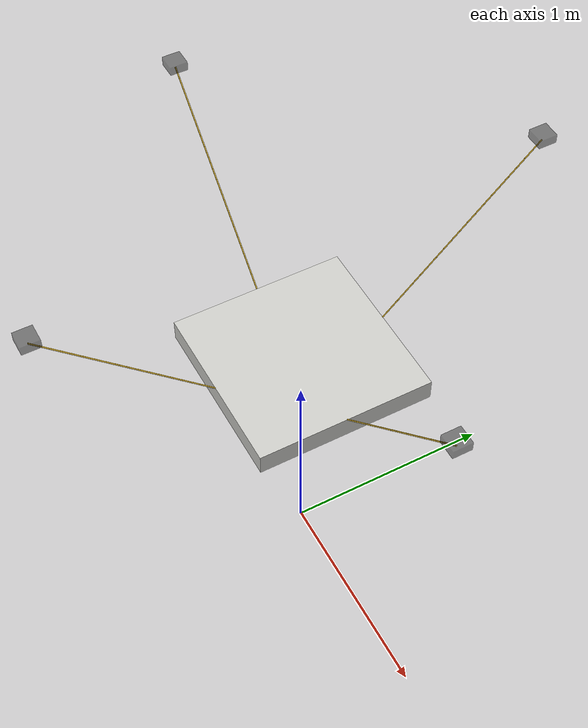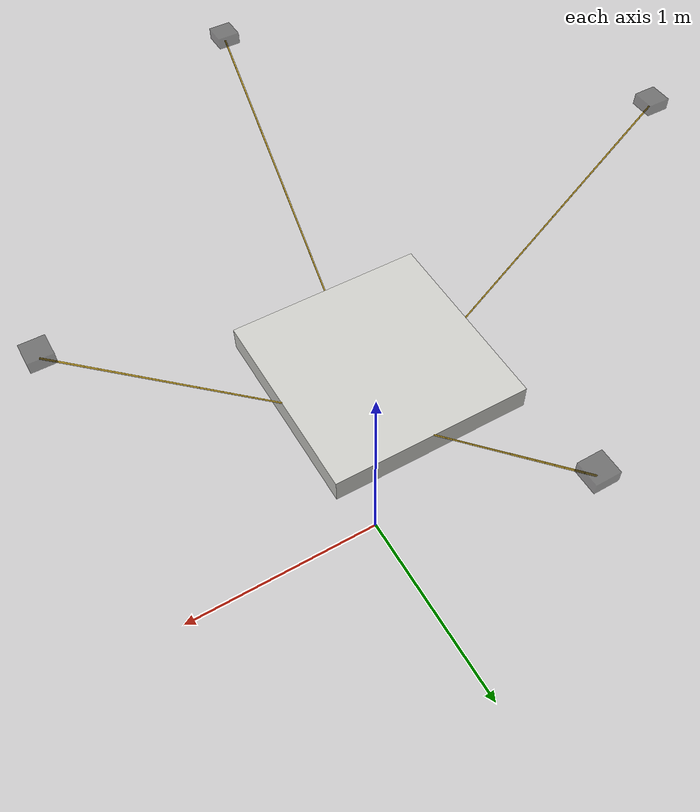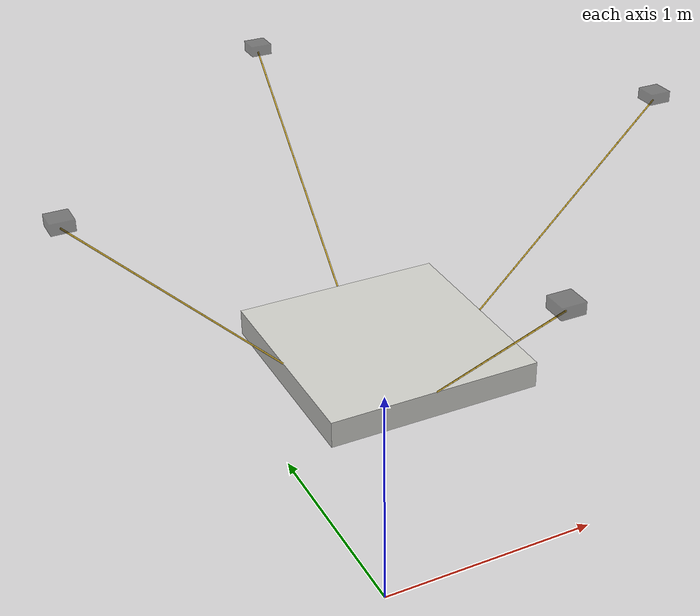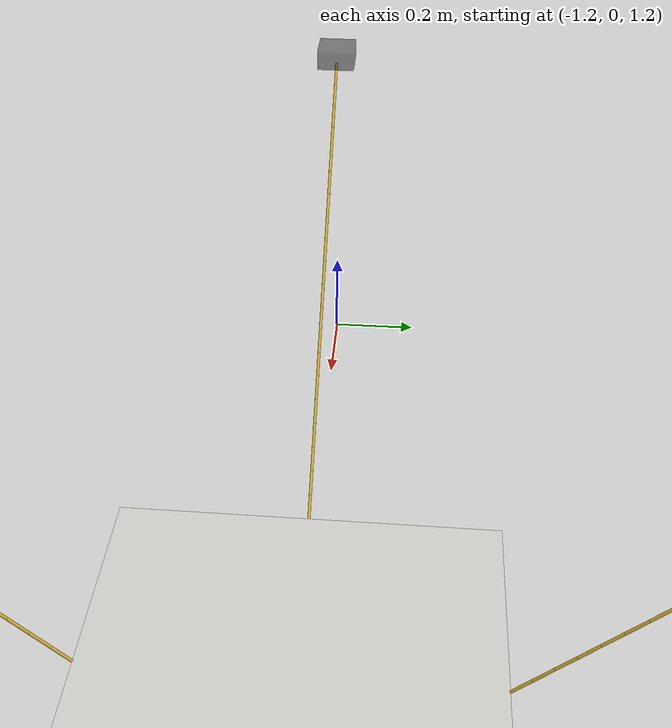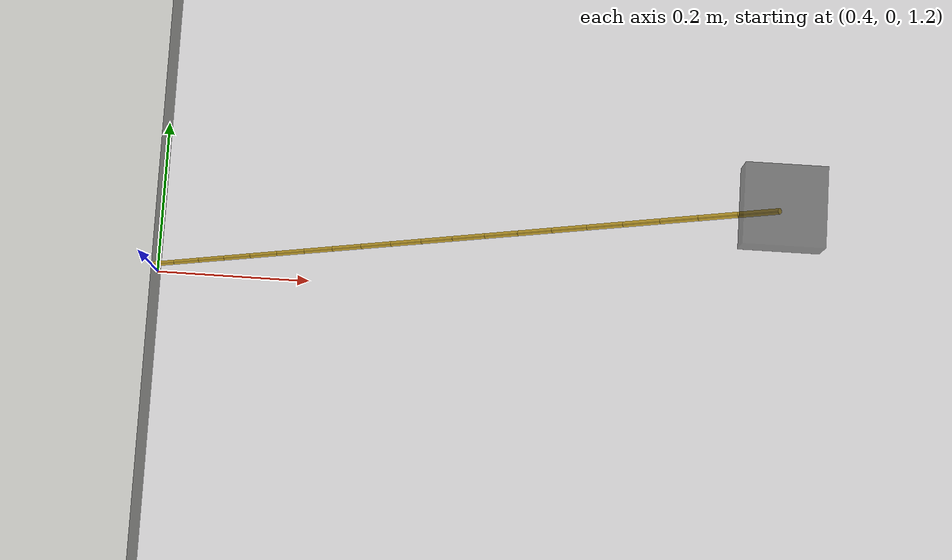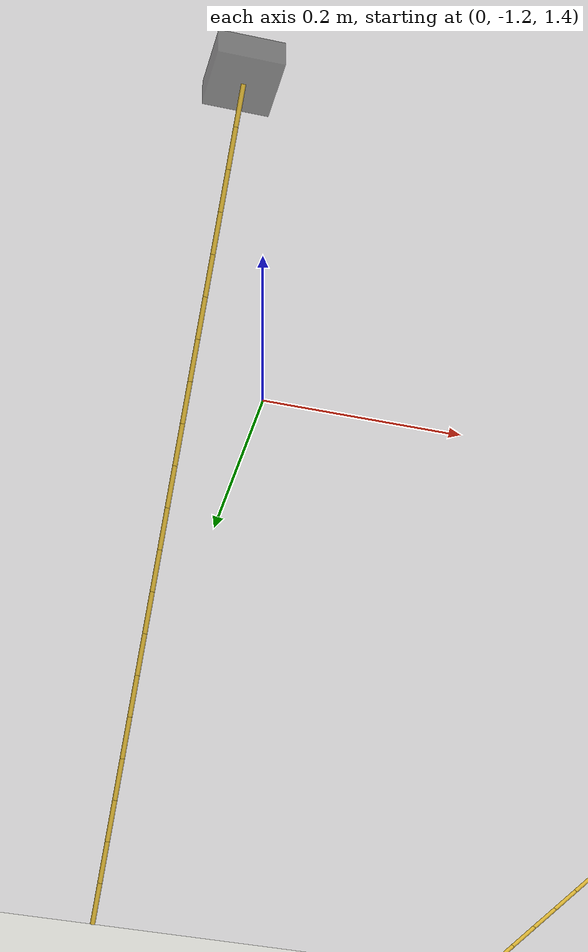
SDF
<?xml version="1.0" ?>
<sdf version='1.7'>

  <!-- Record:
      Oct22:最后一个cylinder是fixed到payload上, segment=5..时会不稳定
       Oct23:universal pose调整后不会跑崩
   -->

  <model name='flexible_cable'>

  <!-- Color properties -->

  <!-- Segment Constants -->

  <!-- base_link initialization -->

  <!-- Elasiticity Params -->

    <!-- 根据绳子数量平均初始化不同base_link的坐标 -->
    <joint name='cable_1_fixed_to_world' type='fixed'>
      <pose relative_to='__model__'>
      1.1071067811865474
      -6.779073879472172e-17
      2.0
      0
      0
      1.5707963267948966
      </pose>
      <parent>world</parent>
      <child>cable_1_base_link</child>
    </joint>

    <link name='cable_1_base_link'>
      <pose relative_to='cable_1_fixed_to_world'>0 0 0 0 -0 0</pose>
      <inertial>
        <mass>0.1</mass>
        <inertia>
          <ixx>0.01</ixx>
          <ixy>0</ixy>
          <ixz>0</ixz>
          <iyy>0.01</iyy>
          <iyz>0</iyz>
          <izz>0.01</izz>
        </inertia>
      </inertial>

      <collision name='cable_1_base_link_collision'>
        <geometry>
          <box>
            <size>0.08 0.08 0.04</size>
          </box>
        </geometry>
        <surface>
          <contact>
            <ode/>
          </contact>
          <friction>
            <ode/>
          </friction>
        </surface>
      </collision>

      <visual name='cable_1_base_link_visual'>
        <geometry>
          <box>
            <size>0.08 0.08 0.04</size>
          </box>
        </geometry>
        <material>
          <script>
            <name>Gazebo/BlackTransparent</name>
            <uri>file://media/materials/scripts/gazebo.material</uri>
          </script>
        </material>
      </visual>
      <self_collide>0</self_collide>
    </link>

    <!-- Generate the first segment LINKED TO base_link -->
    <joint name="cable_1_segment_0_UNIVERSAL" type="universal">
        <child>cable_1_segment_0_cylinder_1</child>
        <parent>cable_1_base_link</parent>
        <pose relative_to='cable_1_base_link'>
        0 0 -0.02 0.7853981633974483 0 0</pose>
        <!-- 增加绳子的偏转角 -->

        <axis>
          <xyz>0 1 0</xyz>
        </axis>
        <axis2>
          <xyz>1 0 0</xyz>
        </axis2>
    </joint>

    <link name='cable_1_segment_0_cylinder_1'>
      <pose relative_to='cable_1_segment_0_UNIVERSAL'>0 0 -0.025 0 -0 0</pose>

      <inertial>
        <mass>0.01</mass>
        <inertia>
          <ixx>2.1058333333333336e-06</ixx>
          <ixy>0</ixy>
          <ixz>0</ixz>
          <iyy>2.1058333333333336e-06</iyy>
          <iyz>0</iyz>
          <izz>4.5e-08</izz>
        </inertia>
      </inertial>

      <collision name='cable_1_segment_0_cylinder_1_collision'>
        <geometry>
          <cylinder>
            <length>0.05</length>
            <radius>0.003</radius>
          </cylinder>
        </geometry>
        <surface>
          <contact>
            <ode/>
          </contact>
          <friction>
            <ode/>
          </friction>
        </surface>
      </collision>

      <visual name='cable_1_segment_0_cylinder_1_visual'>
        <geometry>
          <cylinder>
            <length>0.05</length>
            <radius>0.003</radius>
          </cylinder>
        </geometry>
        <material>
          <script>
            <name>Gazebo/Gold</name>
            <uri>file://media/materials/scripts/gazebo.material</uri>
          </script>
        </material>
      </visual>
      <self_collide>0</self_collide>
      <gravity>1</gravity>
    </link>

    <joint name="cable_1_prismatic_segment_0" type="prismatic">
        <child>cable_1_segment_0_cylinder_2</child>
        <parent>cable_1_segment_0_cylinder_1</parent>
        <pose>0 0 0 0 -0 0</pose>

        <axis>
            <xyz>0.0 0.0 1.0</xyz>
            <limit>
                <effort>-1</effort>
            </limit>
            <dynamics>
              <spring_stiffness>100000.0</spring_stiffness>
              <spring_reference>0.0</spring_reference>
              <damping>0.0</damping>
              <friction>0.0</friction>
            </dynamics>
        </axis>
        <physics>
        <provide_feedback>1</provide_feedback>
        <ode>
          <implicit_spring_damper>1</implicit_spring_damper>
          <cfm_damping>1</cfm_damping>
          <limit>
            <cfm>0</cfm>
            <erp>0.2</erp>
          </limit>
        </ode>
      </physics>
    </joint>

    <link name='cable_1_segment_0_cylinder_2'>
      <pose relative_to='cable_1_segment_0_UNIVERSAL'>0 0 -0.07500000000000001 0 -0 0</pose>

      <inertial>
        <mass>0.01</mass>
        <inertia>
          <ixx>2.1058333333333336e-06</ixx>
          <ixy>0</ixy>
          <ixz>0</ixz>
          <iyy>2.1058333333333336e-06</iyy>
          <iyz>0</iyz>
          <izz>4.5e-08</izz>
        </inertia>
      </inertial>

      <collision name='cable_1_segment_0_cylinder_2_collision'>
        <geometry>
          <cylinder>
            <length>0.05</length>
            <radius>0.003</radius>
          </cylinder>
        </geometry>
        <surface>
          <contact>
            <ode/>
          </contact>
          <friction>
            <ode/>
          </friction>
        </surface>
      </collision>

      <visual name='cable_1_segment_0_cylinder_2_visual'>
        <geometry>
          <cylinder>
            <length>0.05</length>
            <radius>0.003</radius>
          </cylinder>
        </geometry>
        <material>
          <script>
            <name>Gazebo/Gold</name>
            <uri>file://media/materials/scripts/gazebo.material</uri>
          </script>
        </material>
      </visual>
      <self_collide>0</self_collide>
      <gravity>1</gravity>
    </link>

    <!-- No limit set for universal joint-->
    <joint name="cable_1_segment_1_UNIVERSAL" type="universal">
        <child>cable_1_segment_1_cylinder_1</child>
        <parent>cable_1_segment_0_cylinder_2</parent>
        <pose relative_to='cable_1_segment_0_UNIVERSAL'>0 0 -0.1 0 0 0</pose>

        <axis>
          <xyz>0 1 0</xyz>
        </axis>
        <axis2>
          <xyz>1 0 0</xyz>
        </axis2>
    </joint>

    <link name='cable_1_segment_1_cylinder_1'>
      <pose relative_to='cable_1_segment_1_UNIVERSAL'>
      0 0 -0.025 0 -0 0</pose>

      <inertial>
        <mass>0.01</mass>
        <inertia>
          <ixx>2.1058333333333336e-06</ixx>
          <ixy>0</ixy>
          <ixz>0</ixz>
          <iyy>2.1058333333333336e-06</iyy>
          <iyz>0</iyz>
          <izz>4.5e-08</izz>
        </inertia>
      </inertial>

      <collision name='cable_1_segment_1_cylinder_1_collision'>
        <geometry>
          <cylinder>
            <length>0.05</length>
            <radius>0.003</radius>
          </cylinder>
        </geometry>
        <surface>
          <contact>
            <ode/>
          </contact>
          <friction>
            <ode/>
          </friction>
        </surface>
      </collision>

      <visual name='cable_1_segment_1_cylinder_1_visual'>
        <geometry>
          <cylinder>
            <length>0.05</length>
            <radius>0.003</radius>
          </cylinder>
        </geometry>
        <material>
          <script>
            <name>Gazebo/Gold</name>
            <uri>file://media/materials/scripts/gazebo.material</uri>
          </script>
        </material>
      </visual>
      <self_collide>0</self_collide>
      <gravity>1</gravity>
    </link>

    <joint name="cable_1_prismatic_segment_1" type="prismatic">
        <child>cable_1_segment_1_cylinder_2</child>
        <parent>cable_1_segment_1_cylinder_1</parent>
        <pose>0 0 0 0 -0 0</pose>

        <axis>
            <xyz>0.0 0.0 1.0</xyz>
            <limit>
                <effort>-1</effort>
            </limit>
            <dynamics>
              <spring_stiffness>100000.0</spring_stiffness>
              <spring_reference>0.0</spring_reference>
              <damping>0.0</damping>
              <friction>0.0</friction>
            </dynamics>
        </axis>
        <physics>
        <provide_feedback>1</provide_feedback>
        <ode>
          <implicit_spring_damper>1</implicit_spring_damper>
          <cfm_damping>1</cfm_damping>
          <limit>
            <cfm>0</cfm>
            <erp>0.2</erp>
          </limit>
        </ode>
      </physics>

    </joint>

    <link name='cable_1_segment_1_cylinder_2'>
      <pose relative_to='cable_1_segment_1_UNIVERSAL'>
      0 0 -0.07500000000000001 0 -0 0</pose>

      <inertial>
        <mass>0.01</mass>
        <inertia>
          <ixx>2.1058333333333336e-06</ixx>
          <ixy>0</ixy>
          <ixz>0</ixz>
          <iyy>2.1058333333333336e-06</iyy>
          <iyz>0</iyz>
          <izz>4.5e-08</izz>
        </inertia>
      </inertial>

      <collision name='cable_1_segment_1_cylinder_2_collision'>
        <geometry>
          <cylinder>
            <length>0.05</length>
            <radius>0.003</radius>
          </cylinder>
        </geometry>
        <surface>
          <contact>
            <ode/>
          </contact>
          <friction>
            <ode/>
          </friction>
        </surface>
      </collision>

      <visual name='cable_1_segment_1_cylinder_2_visual'>
        <geometry>
          <cylinder>
            <length>0.05</length>
            <radius>0.003</radius>
          </cylinder>
        </geometry>
        <material>
          <script>
            <name>Gazebo/Gold</name>
            <uri>file://media/materials/scripts/gazebo.material</uri>
          </script>
        </material>
      </visual>
      <self_collide>0</self_collide>
      <gravity>1</gravity>
    </link>

    <!-- No limit set for universal joint-->
    <joint name="cable_1_segment_2_UNIVERSAL" type="universal">
        <child>cable_1_segment_2_cylinder_1</child>
        <parent>cable_1_segment_1_cylinder_2</parent>
        <pose relative_to='cable_1_segment_1_UNIVERSAL'>0 0 -0.1 0 0 0</pose>

        <axis>
          <xyz>0 1 0</xyz>
        </axis>
        <axis2>
          <xyz>1 0 0</xyz>
        </axis2>
    </joint>

    <link name='cable_1_segment_2_cylinder_1'>
      <pose relative_to='cable_1_segment_2_UNIVERSAL'>
      0 0 -0.025 0 -0 0</pose>

      <inertial>
        <mass>0.01</mass>
        <inertia>
          <ixx>2.1058333333333336e-06</ixx>
          <ixy>0</ixy>
          <ixz>0</ixz>
          <iyy>2.1058333333333336e-06</iyy>
          <iyz>0</iyz>
          <izz>4.5e-08</izz>
        </inertia>
      </inertial>

      <collision name='cable_1_segment_2_cylinder_1_collision'>
        <geometry>
          <cylinder>
            <length>0.05</length>
            <radius>0.003</radius>
          </cylinder>
        </geometry>
        <surface>
          <contact>
            <ode/>
          </contact>
          <friction>
            <ode/>
          </friction>
        </surface>
      </collision>

      <visual name='cable_1_segment_2_cylinder_1_visual'>
        <geometry>
          <cylinder>
            <length>0.05</length>
            <radius>0.003</radius>
          </cylinder>
        </geometry>
        <material>
          <script>
            <name>Gazebo/Gold</name>
            <uri>file://media/materials/scripts/gazebo.material</uri>
          </script>
        </material>
      </visual>
      <self_collide>0</self_collide>
      <gravity>1</gravity>
    </link>

    <joint name="cable_1_prismatic_segment_2" type="prismatic">
        <child>cable_1_segment_2_cylinder_2</child>
        <parent>cable_1_segment_2_cylinder_1</parent>
        <pose>0 0 0 0 -0 0</pose>

        <axis>
            <xyz>0.0 0.0 1.0</xyz>
            <limit>
                <effort>-1</effort>
            </limit>
            <dynamics>
              <spring_stiffness>100000.0</spring_stiffness>
              <spring_reference>0.0</spring_reference>
              <damping>0.0</damping>
              <friction>0.0</friction>
            </dynamics>
        </axis>
        <physics>
        <provide_feedback>1</provide_feedback>
        <ode>
          <implicit_spring_damper>1</implicit_spring_damper>
          <cfm_damping>1</cfm_damping>
          <limit>
            <cfm>0</cfm>
            <erp>0.2</erp>
          </limit>
        </ode>
      </physics>

    </joint>

    <link name='cable_1_segment_2_cylinder_2'>
      <pose relative_to='cable_1_segment_2_UNIVERSAL'>
      0 0 -0.07500000000000001 0 -0 0</pose>

      <inertial>
        <mass>0.01</mass>
        <inertia>
          <ixx>2.1058333333333336e-06</ixx>
          <ixy>0</ixy>
          <ixz>0</ixz>
          <iyy>2.1058333333333336e-06</iyy>
          <iyz>0</iyz>
          <izz>4.5e-08</izz>
        </inertia>
      </inertial>

      <collision name='cable_1_segment_2_cylinder_2_collision'>
        <geometry>
          <cylinder>
            <length>0.05</length>
            <radius>0.003</radius>
          </cylinder>
        </geometry>
        <surface>
          <contact>
            <ode/>
          </contact>
          <friction>
            <ode/>
          </friction>
        </surface>
      </collision>

      <visual name='cable_1_segment_2_cylinder_2_visual'>
        <geometry>
          <cylinder>
            <length>0.05</length>
            <radius>0.003</radius>
          </cylinder>
        </geometry>
        <material>
          <script>
            <name>Gazebo/Gold</name>
            <uri>file://media/materials/scripts/gazebo.material</uri>
          </script>
        </material>
      </visual>
      <self_collide>0</self_collide>
      <gravity>1</gravity>
    </link>

    <!-- No limit set for universal joint-->
    <joint name="cable_1_segment_3_UNIVERSAL" type="universal">
        <child>cable_1_segment_3_cylinder_1</child>
        <parent>cable_1_segment_2_cylinder_2</parent>
        <pose relative_to='cable_1_segment_2_UNIVERSAL'>0 0 -0.1 0 0 0</pose>

        <axis>
          <xyz>0 1 0</xyz>
        </axis>
        <axis2>
          <xyz>1 0 0</xyz>
        </axis2>
    </joint>

    <link name='cable_1_segment_3_cylinder_1'>
      <pose relative_to='cable_1_segment_3_UNIVERSAL'>
      0 0 -0.025 0 -0 0</pose>

      <inertial>
        <mass>0.01</mass>
        <inertia>
          <ixx>2.1058333333333336e-06</ixx>
          <ixy>0</ixy>
          <ixz>0</ixz>
          <iyy>2.1058333333333336e-06</iyy>
          <iyz>0</iyz>
          <izz>4.5e-08</izz>
        </inertia>
      </inertial>

      <collision name='cable_1_segment_3_cylinder_1_collision'>
        <geometry>
          <cylinder>
            <length>0.05</length>
            <radius>0.003</radius>
          </cylinder>
        </geometry>
        <surface>
          <contact>
            <ode/>
          </contact>
          <friction>
            <ode/>
          </friction>
        </surface>
      </collision>

      <visual name='cable_1_segment_3_cylinder_1_visual'>
        <geometry>
          <cylinder>
            <length>0.05</length>
            <radius>0.003</radius>
          </cylinder>
        </geometry>
        <material>
          <script>
            <name>Gazebo/Gold</name>
            <uri>file://media/materials/scripts/gazebo.material</uri>
          </script>
        </material>
      </visual>
      <self_collide>0</self_collide>
      <gravity>1</gravity>
    </link>

    <joint name="cable_1_prismatic_segment_3" type="prismatic">
        <child>cable_1_segment_3_cylinder_2</child>
        <parent>cable_1_segment_3_cylinder_1</parent>
        <pose>0 0 0 0 -0 0</pose>

        <axis>
            <xyz>0.0 0.0 1.0</xyz>
            <limit>
                <effort>-1</effort>
            </limit>
            <dynamics>
              <spring_stiffness>100000.0</spring_stiffness>
              <spring_reference>0.0</spring_reference>
              <damping>0.0</damping>
              <friction>0.0</friction>
            </dynamics>
        </axis>
        <physics>
        <provide_feedback>1</provide_feedback>
        <ode>
          <implicit_spring_damper>1</implicit_spring_damper>
          <cfm_damping>1</cfm_damping>
          <limit>
            <cfm>0</cfm>
            <erp>0.2</erp>
          </limit>
        </ode>
      </physics>

    </joint>

    <link name='cable_1_segment_3_cylinder_2'>
      <pose relative_to='cable_1_segment_3_UNIVERSAL'>
      0 0 -0.07500000000000001 0 -0 0</pose>

      <inertial>
        <mass>0.01</mass>
        <inertia>
          <ixx>2.1058333333333336e-06</ixx>
          <ixy>0</ixy>
          <ixz>0</ixz>
          <iyy>2.1058333333333336e-06</iyy>
          <iyz>0</iyz>
          <izz>4.5e-08</izz>
        </inertia>
      </inertial>

      <collision name='cable_1_segment_3_cylinder_2_collision'>
        <geometry>
          <cylinder>
            <length>0.05</length>
            <radius>0.003</radius>
          </cylinder>
        </geometry>
        <surface>
          <contact>
            <ode/>
          </contact>
          <friction>
            <ode/>
          </friction>
        </surface>
      </collision>

      <visual name='cable_1_segment_3_cylinder_2_visual'>
        <geometry>
          <cylinder>
            <length>0.05</length>
            <radius>0.003</radius>
          </cylinder>
        </geometry>
        <material>
          <script>
            <name>Gazebo/Gold</name>
            <uri>file://media/materials/scripts/gazebo.material</uri>
          </script>
        </material>
      </visual>
      <self_collide>0</self_collide>
      <gravity>1</gravity>
    </link>

    <!-- No limit set for universal joint-->
    <joint name="cable_1_segment_4_UNIVERSAL" type="universal">
        <child>cable_1_segment_4_cylinder_1</child>
        <parent>cable_1_segment_3_cylinder_2</parent>
        <pose relative_to='cable_1_segment_3_UNIVERSAL'>0 0 -0.1 0 0 0</pose>

        <axis>
          <xyz>0 1 0</xyz>
        </axis>
        <axis2>
          <xyz>1 0 0</xyz>
        </axis2>
    </joint>

    <link name='cable_1_segment_4_cylinder_1'>
      <pose relative_to='cable_1_segment_4_UNIVERSAL'>
      0 0 -0.025 0 -0 0</pose>

      <inertial>
        <mass>0.01</mass>
        <inertia>
          <ixx>2.1058333333333336e-06</ixx>
          <ixy>0</ixy>
          <ixz>0</ixz>
          <iyy>2.1058333333333336e-06</iyy>
          <iyz>0</iyz>
          <izz>4.5e-08</izz>
        </inertia>
      </inertial>

      <collision name='cable_1_segment_4_cylinder_1_collision'>
        <geometry>
          <cylinder>
            <length>0.05</length>
            <radius>0.003</radius>
          </cylinder>
        </geometry>
        <surface>
          <contact>
            <ode/>
          </contact>
          <friction>
            <ode/>
          </friction>
        </surface>
      </collision>

      <visual name='cable_1_segment_4_cylinder_1_visual'>
        <geometry>
          <cylinder>
            <length>0.05</length>
            <radius>0.003</radius>
          </cylinder>
        </geometry>
        <material>
          <script>
            <name>Gazebo/Gold</name>
            <uri>file://media/materials/scripts/gazebo.material</uri>
          </script>
        </material>
      </visual>
      <self_collide>0</self_collide>
      <gravity>1</gravity>
    </link>

    <joint name="cable_1_prismatic_segment_4" type="prismatic">
        <child>cable_1_segment_4_cylinder_2</child>
        <parent>cable_1_segment_4_cylinder_1</parent>
        <pose>0 0 0 0 -0 0</pose>

        <axis>
            <xyz>0.0 0.0 1.0</xyz>
            <limit>
                <effort>-1</effort>
            </limit>
            <dynamics>
              <spring_stiffness>100000.0</spring_stiffness>
              <spring_reference>0.0</spring_reference>
              <damping>0.0</damping>
              <friction>0.0</friction>
            </dynamics>
        </axis>
        <physics>
        <provide_feedback>1</provide_feedback>
        <ode>
          <implicit_spring_damper>1</implicit_spring_damper>
          <cfm_damping>1</cfm_damping>
          <limit>
            <cfm>0</cfm>
            <erp>0.2</erp>
          </limit>
        </ode>
      </physics>

    </joint>

    <link name='cable_1_segment_4_cylinder_2'>
      <pose relative_to='cable_1_segment_4_UNIVERSAL'>
      0 0 -0.07500000000000001 0 -0 0</pose>

      <inertial>
        <mass>0.01</mass>
        <inertia>
          <ixx>2.1058333333333336e-06</ixx>
          <ixy>0</ixy>
          <ixz>0</ixz>
          <iyy>2.1058333333333336e-06</iyy>
          <iyz>0</iyz>
          <izz>4.5e-08</izz>
        </inertia>
      </inertial>

      <collision name='cable_1_segment_4_cylinder_2_collision'>
        <geometry>
          <cylinder>
            <length>0.05</length>
            <radius>0.003</radius>
          </cylinder>
        </geometry>
        <surface>
          <contact>
            <ode/>
          </contact>
          <friction>
            <ode/>
          </friction>
        </surface>
      </collision>

      <visual name='cable_1_segment_4_cylinder_2_visual'>
        <geometry>
          <cylinder>
            <length>0.05</length>
            <radius>0.003</radius>
          </cylinder>
        </geometry>
        <material>
          <script>
            <name>Gazebo/Gold</name>
            <uri>file://media/materials/scripts/gazebo.material</uri>
          </script>
        </material>
      </visual>
      <self_collide>0</self_collide>
      <gravity>1</gravity>
    </link>

    <!-- No limit set for universal joint-->
    <joint name="cable_1_segment_5_UNIVERSAL" type="universal">
        <child>cable_1_segment_5_cylinder_1</child>
        <parent>cable_1_segment_4_cylinder_2</parent>
        <pose relative_to='cable_1_segment_4_UNIVERSAL'>0 0 -0.1 0 0 0</pose>

        <axis>
          <xyz>0 1 0</xyz>
        </axis>
        <axis2>
          <xyz>1 0 0</xyz>
        </axis2>
    </joint>

    <link name='cable_1_segment_5_cylinder_1'>
      <pose relative_to='cable_1_segment_5_UNIVERSAL'>
      0 0 -0.025 0 -0 0</pose>

      <inertial>
        <mass>0.01</mass>
        <inertia>
          <ixx>2.1058333333333336e-06</ixx>
          <ixy>0</ixy>
          <ixz>0</ixz>
          <iyy>2.1058333333333336e-06</iyy>
          <iyz>0</iyz>
          <izz>4.5e-08</izz>
        </inertia>
      </inertial>

      <collision name='cable_1_segment_5_cylinder_1_collision'>
        <geometry>
          <cylinder>
            <length>0.05</length>
            <radius>0.003</radius>
          </cylinder>
        </geometry>
        <surface>
          <contact>
            <ode/>
          </contact>
          <friction>
            <ode/>
          </friction>
        </surface>
      </collision>

      <visual name='cable_1_segment_5_cylinder_1_visual'>
        <geometry>
          <cylinder>
            <length>0.05</length>
            <radius>0.003</radius>
          </cylinder>
        </geometry>
        <material>
          <script>
            <name>Gazebo/Gold</name>
            <uri>file://media/materials/scripts/gazebo.material</uri>
          </script>
        </material>
      </visual>
      <self_collide>0</self_collide>
      <gravity>1</gravity>
    </link>

    <joint name="cable_1_prismatic_segment_5" type="prismatic">
        <child>cable_1_segment_5_cylinder_2</child>
        <parent>cable_1_segment_5_cylinder_1</parent>
        <pose>0 0 0 0 -0 0</pose>

        <axis>
            <xyz>0.0 0.0 1.0</xyz>
            <limit>
                <effort>-1</effort>
            </limit>
            <dynamics>
              <spring_stiffness>100000.0</spring_stiffness>
              <spring_reference>0.0</spring_reference>
              <damping>0.0</damping>
              <friction>0.0</friction>
            </dynamics>
        </axis>
        <physics>
        <provide_feedback>1</provide_feedback>
        <ode>
          <implicit_spring_damper>1</implicit_spring_damper>
          <cfm_damping>1</cfm_damping>
          <limit>
            <cfm>0</cfm>
            <erp>0.2</erp>
          </limit>
        </ode>
      </physics>

    </joint>

    <link name='cable_1_segment_5_cylinder_2'>
      <pose relative_to='cable_1_segment_5_UNIVERSAL'>
      0 0 -0.07500000000000001 0 -0 0</pose>

      <inertial>
        <mass>0.01</mass>
        <inertia>
          <ixx>2.1058333333333336e-06</ixx>
          <ixy>0</ixy>
          <ixz>0</ixz>
          <iyy>2.1058333333333336e-06</iyy>
          <iyz>0</iyz>
          <izz>4.5e-08</izz>
        </inertia>
      </inertial>

      <collision name='cable_1_segment_5_cylinder_2_collision'>
        <geometry>
          <cylinder>
            <length>0.05</length>
            <radius>0.003</radius>
          </cylinder>
        </geometry>
        <surface>
          <contact>
            <ode/>
          </contact>
          <friction>
            <ode/>
          </friction>
        </surface>
      </collision>

      <visual name='cable_1_segment_5_cylinder_2_visual'>
        <geometry>
          <cylinder>
            <length>0.05</length>
            <radius>0.003</radius>
          </cylinder>
        </geometry>
        <material>
          <script>
            <name>Gazebo/Gold</name>
            <uri>file://media/materials/scripts/gazebo.material</uri>
          </script>
        </material>
      </visual>
      <self_collide>0</self_collide>
      <gravity>1</gravity>
    </link>

    <!-- No limit set for universal joint-->
    <joint name="cable_1_segment_6_UNIVERSAL" type="universal">
        <child>cable_1_segment_6_cylinder_1</child>
        <parent>cable_1_segment_5_cylinder_2</parent>
        <pose relative_to='cable_1_segment_5_UNIVERSAL'>0 0 -0.1 0 0 0</pose>

        <axis>
          <xyz>0 1 0</xyz>
        </axis>
        <axis2>
          <xyz>1 0 0</xyz>
        </axis2>
    </joint>

    <link name='cable_1_segment_6_cylinder_1'>
      <pose relative_to='cable_1_segment_6_UNIVERSAL'>
      0 0 -0.025 0 -0 0</pose>

      <inertial>
        <mass>0.01</mass>
        <inertia>
          <ixx>2.1058333333333336e-06</ixx>
          <ixy>0</ixy>
          <ixz>0</ixz>
          <iyy>2.1058333333333336e-06</iyy>
          <iyz>0</iyz>
          <izz>4.5e-08</izz>
        </inertia>
      </inertial>

      <collision name='cable_1_segment_6_cylinder_1_collision'>
        <geometry>
          <cylinder>
            <length>0.05</length>
            <radius>0.003</radius>
          </cylinder>
        </geometry>
        <surface>
          <contact>
            <ode/>
          </contact>
          <friction>
            <ode/>
          </friction>
        </surface>
      </collision>

      <visual name='cable_1_segment_6_cylinder_1_visual'>
        <geometry>
          <cylinder>
            <length>0.05</length>
            <radius>0.003</radius>
          </cylinder>
        </geometry>
        <material>
          <script>
            <name>Gazebo/Gold</name>
            <uri>file://media/materials/scripts/gazebo.material</uri>
          </script>
        </material>
      </visual>
      <self_collide>0</self_collide>
      <gravity>1</gravity>
    </link>

    <joint name="cable_1_prismatic_segment_6" type="prismatic">
        <child>cable_1_segment_6_cylinder_2</child>
        <parent>cable_1_segment_6_cylinder_1</parent>
        <pose>0 0 0 0 -0 0</pose>

        <axis>
            <xyz>0.0 0.0 1.0</xyz>
            <limit>
                <effort>-1</effort>
            </limit>
            <dynamics>
              <spring_stiffness>100000.0</spring_stiffness>
              <spring_reference>0.0</spring_reference>
              <damping>0.0</damping>
              <friction>0.0</friction>
            </dynamics>
        </axis>
        <physics>
        <provide_feedback>1</provide_feedback>
        <ode>
          <implicit_spring_damper>1</implicit_spring_damper>
          <cfm_damping>1</cfm_damping>
          <limit>
            <cfm>0</cfm>
            <erp>0.2</erp>
          </limit>
        </ode>
      </physics>

    </joint>

    <link name='cable_1_segment_6_cylinder_2'>
      <pose relative_to='cable_1_segment_6_UNIVERSAL'>
      0 0 -0.07500000000000001 0 -0 0</pose>

      <inertial>
        <mass>0.01</mass>
        <inertia>
          <ixx>2.1058333333333336e-06</ixx>
          <ixy>0</ixy>
          <ixz>0</ixz>
          <iyy>2.1058333333333336e-06</iyy>
          <iyz>0</iyz>
          <izz>4.5e-08</izz>
        </inertia>
      </inertial>

      <collision name='cable_1_segment_6_cylinder_2_collision'>
        <geometry>
          <cylinder>
            <length>0.05</length>
            <radius>0.003</radius>
          </cylinder>
        </geometry>
        <surface>
          <contact>
            <ode/>
          </contact>
          <friction>
            <ode/>
          </friction>
        </surface>
      </collision>

      <visual name='cable_1_segment_6_cylinder_2_visual'>
        <geometry>
          <cylinder>
            <length>0.05</length>
            <radius>0.003</radius>
          </cylinder>
        </geometry>
        <material>
          <script>
            <name>Gazebo/Gold</name>
            <uri>file://media/materials/scripts/gazebo.material</uri>
          </script>
        </material>
      </visual>
      <self_collide>0</self_collide>
      <gravity>1</gravity>
    </link>

    <!-- No limit set for universal joint-->
    <joint name="cable_1_segment_7_UNIVERSAL" type="universal">
        <child>cable_1_segment_7_cylinder_1</child>
        <parent>cable_1_segment_6_cylinder_2</parent>
        <pose relative_to='cable_1_segment_6_UNIVERSAL'>0 0 -0.1 0 0 0</pose>

        <axis>
          <xyz>0 1 0</xyz>
        </axis>
        <axis2>
          <xyz>1 0 0</xyz>
        </axis2>
    </joint>

    <link name='cable_1_segment_7_cylinder_1'>
      <pose relative_to='cable_1_segment_7_UNIVERSAL'>
      0 0 -0.025 0 -0 0</pose>

      <inertial>
        <mass>0.01</mass>
        <inertia>
          <ixx>2.1058333333333336e-06</ixx>
          <ixy>0</ixy>
          <ixz>0</ixz>
          <iyy>2.1058333333333336e-06</iyy>
          <iyz>0</iyz>
          <izz>4.5e-08</izz>
        </inertia>
      </inertial>

      <collision name='cable_1_segment_7_cylinder_1_collision'>
        <geometry>
          <cylinder>
            <length>0.05</length>
            <radius>0.003</radius>
          </cylinder>
        </geometry>
        <surface>
          <contact>
            <ode/>
          </contact>
          <friction>
            <ode/>
          </friction>
        </surface>
      </collision>

      <visual name='cable_1_segment_7_cylinder_1_visual'>
        <geometry>
          <cylinder>
            <length>0.05</length>
            <radius>0.003</radius>
          </cylinder>
        </geometry>
        <material>
          <script>
            <name>Gazebo/Gold</name>
            <uri>file://media/materials/scripts/gazebo.material</uri>
          </script>
        </material>
      </visual>
      <self_collide>0</self_collide>
      <gravity>1</gravity>
    </link>

    <joint name="cable_1_prismatic_segment_7" type="prismatic">
        <child>cable_1_segment_7_cylinder_2</child>
        <parent>cable_1_segment_7_cylinder_1</parent>
        <pose>0 0 0 0 -0 0</pose>

        <axis>
            <xyz>0.0 0.0 1.0</xyz>
            <limit>
                <effort>-1</effort>
            </limit>
            <dynamics>
              <spring_stiffness>100000.0</spring_stiffness>
              <spring_reference>0.0</spring_reference>
              <damping>0.0</damping>
              <friction>0.0</friction>
            </dynamics>
        </axis>
        <physics>
        <provide_feedback>1</provide_feedback>
        <ode>
          <implicit_spring_damper>1</implicit_spring_damper>
          <cfm_damping>1</cfm_damping>
          <limit>
            <cfm>0</cfm>
            <erp>0.2</erp>
          </limit>
        </ode>
      </physics>

    </joint>

    <link name='cable_1_segment_7_cylinder_2'>
      <pose relative_to='cable_1_segment_7_UNIVERSAL'>
      0 0 -0.07500000000000001 0 -0 0</pose>

      <inertial>
        <mass>0.01</mass>
        <inertia>
          <ixx>2.1058333333333336e-06</ixx>
          <ixy>0</ixy>
          <ixz>0</ixz>
          <iyy>2.1058333333333336e-06</iyy>
          <iyz>0</iyz>
          <izz>4.5e-08</izz>
        </inertia>
      </inertial>

      <collision name='cable_1_segment_7_cylinder_2_collision'>
        <geometry>
          <cylinder>
            <length>0.05</length>
            <radius>0.003</radius>
          </cylinder>
        </geometry>
        <surface>
          <contact>
            <ode/>
          </contact>
          <friction>
            <ode/>
          </friction>
        </surface>
      </collision>

      <visual name='cable_1_segment_7_cylinder_2_visual'>
        <geometry>
          <cylinder>
            <length>0.05</length>
            <radius>0.003</radius>
          </cylinder>
        </geometry>
        <material>
          <script>
            <name>Gazebo/Gold</name>
            <uri>file://media/materials/scripts/gazebo.material</uri>
          </script>
        </material>
      </visual>
      <self_collide>0</self_collide>
      <gravity>1</gravity>
    </link>

    <!-- No limit set for universal joint-->
    <joint name="cable_1_segment_8_UNIVERSAL" type="universal">
        <child>cable_1_segment_8_cylinder_1</child>
        <parent>cable_1_segment_7_cylinder_2</parent>
        <pose relative_to='cable_1_segment_7_UNIVERSAL'>0 0 -0.1 0 0 0</pose>

        <axis>
          <xyz>0 1 0</xyz>
        </axis>
        <axis2>
          <xyz>1 0 0</xyz>
        </axis2>
    </joint>

    <link name='cable_1_segment_8_cylinder_1'>
      <pose relative_to='cable_1_segment_8_UNIVERSAL'>
      0 0 -0.025 0 -0 0</pose>

      <inertial>
        <mass>0.01</mass>
        <inertia>
          <ixx>2.1058333333333336e-06</ixx>
          <ixy>0</ixy>
          <ixz>0</ixz>
          <iyy>2.1058333333333336e-06</iyy>
          <iyz>0</iyz>
          <izz>4.5e-08</izz>
        </inertia>
      </inertial>

      <collision name='cable_1_segment_8_cylinder_1_collision'>
        <geometry>
          <cylinder>
            <length>0.05</length>
            <radius>0.003</radius>
          </cylinder>
        </geometry>
        <surface>
          <contact>
            <ode/>
          </contact>
          <friction>
            <ode/>
          </friction>
        </surface>
      </collision>

      <visual name='cable_1_segment_8_cylinder_1_visual'>
        <geometry>
          <cylinder>
            <length>0.05</length>
            <radius>0.003</radius>
          </cylinder>
        </geometry>
        <material>
          <script>
            <name>Gazebo/Gold</name>
            <uri>file://media/materials/scripts/gazebo.material</uri>
          </script>
        </material>
      </visual>
      <self_collide>0</self_collide>
      <gravity>1</gravity>
    </link>

    <joint name="cable_1_prismatic_segment_8" type="prismatic">
        <child>cable_1_segment_8_cylinder_2</child>
        <parent>cable_1_segment_8_cylinder_1</parent>
        <pose>0 0 0 0 -0 0</pose>

        <axis>
            <xyz>0.0 0.0 1.0</xyz>
            <limit>
                <effort>-1</effort>
            </limit>
            <dynamics>
              <spring_stiffness>100000.0</spring_stiffness>
              <spring_reference>0.0</spring_reference>
              <damping>0.0</damping>
              <friction>0.0</friction>
            </dynamics>
        </axis>
        <physics>
        <provide_feedback>1</provide_feedback>
        <ode>
          <implicit_spring_damper>1</implicit_spring_damper>
          <cfm_damping>1</cfm_damping>
          <limit>
            <cfm>0</cfm>
            <erp>0.2</erp>
          </limit>
        </ode>
      </physics>

    </joint>

    <link name='cable_1_segment_8_cylinder_2'>
      <pose relative_to='cable_1_segment_8_UNIVERSAL'>
      0 0 -0.07500000000000001 0 -0 0</pose>

      <inertial>
        <mass>0.01</mass>
        <inertia>
          <ixx>2.1058333333333336e-06</ixx>
          <ixy>0</ixy>
          <ixz>0</ixz>
          <iyy>2.1058333333333336e-06</iyy>
          <iyz>0</iyz>
          <izz>4.5e-08</izz>
        </inertia>
      </inertial>

      <collision name='cable_1_segment_8_cylinder_2_collision'>
        <geometry>
          <cylinder>
            <length>0.05</length>
            <radius>0.003</radius>
          </cylinder>
        </geometry>
        <surface>
          <contact>
            <ode/>
          </contact>
          <friction>
            <ode/>
          </friction>
        </surface>
      </collision>

      <visual name='cable_1_segment_8_cylinder_2_visual'>
        <geometry>
          <cylinder>
            <length>0.05</length>
            <radius>0.003</radius>
          </cylinder>
        </geometry>
        <material>
          <script>
            <name>Gazebo/Gold</name>
            <uri>file://media/materials/scripts/gazebo.material</uri>
          </script>
        </material>
      </visual>
      <self_collide>0</self_collide>
      <gravity>1</gravity>
    </link>

    <!-- No limit set for universal joint-->
    <joint name="cable_1_segment_9_UNIVERSAL" type="universal">
        <child>cable_1_segment_9_cylinder_1</child>
        <parent>cable_1_segment_8_cylinder_2</parent>
        <pose relative_to='cable_1_segment_8_UNIVERSAL'>0 0 -0.1 0 0 0</pose>

        <axis>
          <xyz>0 1 0</xyz>
        </axis>
        <axis2>
          <xyz>1 0 0</xyz>
        </axis2>
    </joint>

    <link name='cable_1_segment_9_cylinder_1'>
      <pose relative_to='cable_1_segment_9_UNIVERSAL'>
      0 0 -0.025 0 -0 0</pose>

      <inertial>
        <mass>0.01</mass>
        <inertia>
          <ixx>2.1058333333333336e-06</ixx>
          <ixy>0</ixy>
          <ixz>0</ixz>
          <iyy>2.1058333333333336e-06</iyy>
          <iyz>0</iyz>
          <izz>4.5e-08</izz>
        </inertia>
      </inertial>

      <collision name='cable_1_segment_9_cylinder_1_collision'>
        <geometry>
          <cylinder>
            <length>0.05</length>
            <radius>0.003</radius>
          </cylinder>
        </geometry>
        <surface>
          <contact>
            <ode/>
          </contact>
          <friction>
            <ode/>
          </friction>
        </surface>
      </collision>

      <visual name='cable_1_segment_9_cylinder_1_visual'>
        <geometry>
          <cylinder>
            <length>0.05</length>
            <radius>0.003</radius>
          </cylinder>
        </geometry>
        <material>
          <script>
            <name>Gazebo/Gold</name>
            <uri>file://media/materials/scripts/gazebo.material</uri>
          </script>
        </material>
      </visual>
      <self_collide>0</self_collide>
      <gravity>1</gravity>
    </link>

    <joint name="cable_1_prismatic_segment_9" type="prismatic">
        <child>cable_1_segment_9_cylinder_2</child>
        <parent>cable_1_segment_9_cylinder_1</parent>
        <pose>0 0 0 0 -0 0</pose>

        <axis>
            <xyz>0.0 0.0 1.0</xyz>
            <limit>
                <effort>-1</effort>
            </limit>
            <dynamics>
              <spring_stiffness>100000.0</spring_stiffness>
              <spring_reference>0.0</spring_reference>
              <damping>0.0</damping>
              <friction>0.0</friction>
            </dynamics>
        </axis>
        <physics>
        <provide_feedback>1</provide_feedback>
        <ode>
          <implicit_spring_damper>1</implicit_spring_damper>
          <cfm_damping>1</cfm_damping>
          <limit>
            <cfm>0</cfm>
            <erp>0.2</erp>
          </limit>
        </ode>
      </physics>

    </joint>

    <link name='cable_1_segment_9_cylinder_2'>
      <pose relative_to='cable_1_segment_9_UNIVERSAL'>
      0 0 -0.07500000000000001 0 -0 0</pose>

      <inertial>
        <mass>0.01</mass>
        <inertia>
          <ixx>2.1058333333333336e-06</ixx>
          <ixy>0</ixy>
          <ixz>0</ixz>
          <iyy>2.1058333333333336e-06</iyy>
          <iyz>0</iyz>
          <izz>4.5e-08</izz>
        </inertia>
      </inertial>

      <collision name='cable_1_segment_9_cylinder_2_collision'>
        <geometry>
          <cylinder>
            <length>0.05</length>
            <radius>0.003</radius>
          </cylinder>
        </geometry>
        <surface>
          <contact>
            <ode/>
          </contact>
          <friction>
            <ode/>
          </friction>
        </surface>
      </collision>

      <visual name='cable_1_segment_9_cylinder_2_visual'>
        <geometry>
          <cylinder>
            <length>0.05</length>
            <radius>0.003</radius>
          </cylinder>
        </geometry>
        <material>
          <script>
            <name>Gazebo/Gold</name>
            <uri>file://media/materials/scripts/gazebo.material</uri>
          </script>
        </material>
      </visual>
      <self_collide>0</self_collide>
      <gravity>1</gravity>
    </link>

    <!-- End JOINT to connect cable and paload -->
    <joint name="cable_1_endjoint" type="universal">
        <child>payload</child>
        <parent>cable_1_segment_9_cylinder_2</parent>
        <pose relative_to='cable_1_segment_9_cylinder_2'>
        0.0 0.0 -0.07500000000000001 0.0 0.0 0.0
        </pose>
        <axis>
          <xyz>1 0 0</xyz>
        </axis>
        <axis2>
          <xyz>0 1 0</xyz>
        </axis2>
    </joint>

    <!-- 根据绳子数量平均初始化不同base_link的坐标 -->
    <joint name='cable_2_fixed_to_world' type='fixed'>
      <pose relative_to='__model__'>
      1.3558147758944345e-16
      1.1071067811865474
      2.0
      0
      0
      3.141592653589793
      </pose>
      <parent>world</parent>
      <child>cable_2_base_link</child>
    </joint>

    <link name='cable_2_base_link'>
      <pose relative_to='cable_2_fixed_to_world'>0 0 0 0 -0 0</pose>
      <inertial>
        <mass>0.1</mass>
        <inertia>
          <ixx>0.01</ixx>
          <ixy>0</ixy>
          <ixz>0</ixz>
          <iyy>0.01</iyy>
          <iyz>0</iyz>
          <izz>0.01</izz>
        </inertia>
      </inertial>

      <collision name='cable_2_base_link_collision'>
        <geometry>
          <box>
            <size>0.08 0.08 0.04</size>
          </box>
        </geometry>
        <surface>
          <contact>
            <ode/>
          </contact>
          <friction>
            <ode/>
          </friction>
        </surface>
      </collision>

      <visual name='cable_2_base_link_visual'>
        <geometry>
          <box>
            <size>0.08 0.08 0.04</size>
          </box>
        </geometry>
        <material>
          <script>
            <name>Gazebo/BlackTransparent</name>
            <uri>file://media/materials/scripts/gazebo.material</uri>
          </script>
        </material>
      </visual>
      <self_collide>0</self_collide>
    </link>

    <!-- Generate the first segment LINKED TO base_link -->
    <joint name="cable_2_segment_0_UNIVERSAL" type="universal">
        <child>cable_2_segment_0_cylinder_1</child>
        <parent>cable_2_base_link</parent>
        <pose relative_to='cable_2_base_link'>
        0 0 -0.02 0.7853981633974483 0 0</pose>
        <!-- 增加绳子的偏转角 -->

        <axis>
          <xyz>0 1 0</xyz>
        </axis>
        <axis2>
          <xyz>1 0 0</xyz>
        </axis2>
    </joint>

    <link name='cable_2_segment_0_cylinder_1'>
      <pose relative_to='cable_2_segment_0_UNIVERSAL'>0 0 -0.025 0 -0 0</pose>

      <inertial>
        <mass>0.01</mass>
        <inertia>
          <ixx>2.1058333333333336e-06</ixx>
          <ixy>0</ixy>
          <ixz>0</ixz>
          <iyy>2.1058333333333336e-06</iyy>
          <iyz>0</iyz>
          <izz>4.5e-08</izz>
        </inertia>
      </inertial>

      <collision name='cable_2_segment_0_cylinder_1_collision'>
        <geometry>
          <cylinder>
            <length>0.05</length>
            <radius>0.003</radius>
          </cylinder>
        </geometry>
        <surface>
          <contact>
            <ode/>
          </contact>
          <friction>
            <ode/>
          </friction>
        </surface>
      </collision>

      <visual name='cable_2_segment_0_cylinder_1_visual'>
        <geometry>
          <cylinder>
            <length>0.05</length>
            <radius>0.003</radius>
          </cylinder>
        </geometry>
        <material>
          <script>
            <name>Gazebo/Gold</name>
            <uri>file://media/materials/scripts/gazebo.material</uri>
          </script>
        </material>
      </visual>
      <self_collide>0</self_collide>
      <gravity>1</gravity>
    </link>

    <joint name="cable_2_prismatic_segment_0" type="prismatic">
        <child>cable_2_segment_0_cylinder_2</child>
        <parent>cable_2_segment_0_cylinder_1</parent>
        <pose>0 0 0 0 -0 0</pose>

        <axis>
            <xyz>0.0 0.0 1.0</xyz>
            <limit>
                <effort>-1</effort>
            </limit>
            <dynamics>
              <spring_stiffness>100000.0</spring_stiffness>
              <spring_reference>0.0</spring_reference>
              <damping>0.0</damping>
              <friction>0.0</friction>
            </dynamics>
        </axis>
        <physics>
        <provide_feedback>1</provide_feedback>
        <ode>
          <implicit_spring_damper>1</implicit_spring_damper>
          <cfm_damping>1</cfm_damping>
          <limit>
            <cfm>0</cfm>
            <erp>0.2</erp>
          </limit>
        </ode>
      </physics>
    </joint>

    <link name='cable_2_segment_0_cylinder_2'>
      <pose relative_to='cable_2_segment_0_UNIVERSAL'>0 0 -0.07500000000000001 0 -0 0</pose>

      <inertial>
        <mass>0.01</mass>
        <inertia>
          <ixx>2.1058333333333336e-06</ixx>
          <ixy>0</ixy>
          <ixz>0</ixz>
          <iyy>2.1058333333333336e-06</iyy>
          <iyz>0</iyz>
          <izz>4.5e-08</izz>
        </inertia>
      </inertial>

      <collision name='cable_2_segment_0_cylinder_2_collision'>
        <geometry>
          <cylinder>
            <length>0.05</length>
            <radius>0.003</radius>
          </cylinder>
        </geometry>
        <surface>
          <contact>
            <ode/>
          </contact>
          <friction>
            <ode/>
          </friction>
        </surface>
      </collision>

      <visual name='cable_2_segment_0_cylinder_2_visual'>
        <geometry>
          <cylinder>
            <length>0.05</length>
            <radius>0.003</radius>
          </cylinder>
        </geometry>
        <material>
          <script>
            <name>Gazebo/Gold</name>
            <uri>file://media/materials/scripts/gazebo.material</uri>
          </script>
        </material>
      </visual>
      <self_collide>0</self_collide>
      <gravity>1</gravity>
    </link>

    <!-- No limit set for universal joint-->
    <joint name="cable_2_segment_1_UNIVERSAL" type="universal">
        <child>cable_2_segment_1_cylinder_1</child>
        <parent>cable_2_segment_0_cylinder_2</parent>
        <pose relative_to='cable_2_segment_0_UNIVERSAL'>0 0 -0.1 0 0 0</pose>

        <axis>
          <xyz>0 1 0</xyz>
        </axis>
        <axis2>
          <xyz>1 0 0</xyz>
        </axis2>
    </joint>

    <link name='cable_2_segment_1_cylinder_1'>
      <pose relative_to='cable_2_segment_1_UNIVERSAL'>
      0 0 -0.025 0 -0 0</pose>

      <inertial>
        <mass>0.01</mass>
        <inertia>
          <ixx>2.1058333333333336e-06</ixx>
          <ixy>0</ixy>
          <ixz>0</ixz>
          <iyy>2.1058333333333336e-06</iyy>
          <iyz>0</iyz>
          <izz>4.5e-08</izz>
        </inertia>
      </inertial>

      <collision name='cable_2_segment_1_cylinder_1_collision'>
        <geometry>
          <cylinder>
            <length>0.05</length>
            <radius>0.003</radius>
          </cylinder>
        </geometry>
        <surface>
          <contact>
            <ode/>
          </contact>
          <friction>
            <ode/>
          </friction>
        </surface>
      </collision>

      <visual name='cable_2_segment_1_cylinder_1_visual'>
        <geometry>
          <cylinder>
            <length>0.05</length>
            <radius>0.003</radius>
          </cylinder>
        </geometry>
        <material>
          <script>
            <name>Gazebo/Gold</name>
            <uri>file://media/materials/scripts/gazebo.material</uri>
          </script>
        </material>
      </visual>
      <self_collide>0</self_collide>
      <gravity>1</gravity>
    </link>

    <joint name="cable_2_prismatic_segment_1" type="prismatic">
        <child>cable_2_segment_1_cylinder_2</child>
        <parent>cable_2_segment_1_cylinder_1</parent>
        <pose>0 0 0 0 -0 0</pose>

        <axis>
            <xyz>0.0 0.0 1.0</xyz>
            <limit>
                <effort>-1</effort>
            </limit>
            <dynamics>
              <spring_stiffness>100000.0</spring_stiffness>
              <spring_reference>0.0</spring_reference>
              <damping>0.0</damping>
              <friction>0.0</friction>
            </dynamics>
        </axis>
        <physics>
        <provide_feedback>1</provide_feedback>
        <ode>
          <implicit_spring_damper>1</implicit_spring_damper>
          <cfm_damping>1</cfm_damping>
          <limit>
            <cfm>0</cfm>
            <erp>0.2</erp>
          </limit>
        </ode>
      </physics>

    </joint>

    <link name='cable_2_segment_1_cylinder_2'>
      <pose relative_to='cable_2_segment_1_UNIVERSAL'>
      0 0 -0.07500000000000001 0 -0 0</pose>

      <inertial>
        <mass>0.01</mass>
        <inertia>
          <ixx>2.1058333333333336e-06</ixx>
          <ixy>0</ixy>
          <ixz>0</ixz>
          <iyy>2.1058333333333336e-06</iyy>
          <iyz>0</iyz>
          <izz>4.5e-08</izz>
        </inertia>
      </inertial>

      <collision name='cable_2_segment_1_cylinder_2_collision'>
        <geometry>
          <cylinder>
            <length>0.05</length>
            <radius>0.003</radius>
          </cylinder>
        </geometry>
        <surface>
          <contact>
            <ode/>
          </contact>
          <friction>
            <ode/>
          </friction>
        </surface>
      </collision>

      <visual name='cable_2_segment_1_cylinder_2_visual'>
        <geometry>
          <cylinder>
            <length>0.05</length>
            <radius>0.003</radius>
          </cylinder>
        </geometry>
        <material>
          <script>
            <name>Gazebo/Gold</name>
            <uri>file://media/materials/scripts/gazebo.material</uri>
          </script>
        </material>
      </visual>
      <self_collide>0</self_collide>
      <gravity>1</gravity>
    </link>

    <!-- No limit set for universal joint-->
    <joint name="cable_2_segment_2_UNIVERSAL" type="universal">
        <child>cable_2_segment_2_cylinder_1</child>
        <parent>cable_2_segment_1_cylinder_2</parent>
        <pose relative_to='cable_2_segment_1_UNIVERSAL'>0 0 -0.1 0 0 0</pose>

        <axis>
          <xyz>0 1 0</xyz>
        </axis>
        <axis2>
          <xyz>1 0 0</xyz>
        </axis2>
    </joint>

    <link name='cable_2_segment_2_cylinder_1'>
      <pose relative_to='cable_2_segment_2_UNIVERSAL'>
      0 0 -0.025 0 -0 0</pose>

      <inertial>
        <mass>0.01</mass>
        <inertia>
          <ixx>2.1058333333333336e-06</ixx>
          <ixy>0</ixy>
          <ixz>0</ixz>
          <iyy>2.1058333333333336e-06</iyy>
          <iyz>0</iyz>
          <izz>4.5e-08</izz>
        </inertia>
      </inertial>

      <collision name='cable_2_segment_2_cylinder_1_collision'>
        <geometry>
          <cylinder>
            <length>0.05</length>
            <radius>0.003</radius>
          </cylinder>
        </geometry>
        <surface>
          <contact>
            <ode/>
          </contact>
          <friction>
            <ode/>
          </friction>
        </surface>
      </collision>

      <visual name='cable_2_segment_2_cylinder_1_visual'>
        <geometry>
          <cylinder>
            <length>0.05</length>
            <radius>0.003</radius>
          </cylinder>
        </geometry>
        <material>
          <script>
            <name>Gazebo/Gold</name>
            <uri>file://media/materials/scripts/gazebo.material</uri>
          </script>
        </material>
      </visual>
      <self_collide>0</self_collide>
      <gravity>1</gravity>
    </link>

    <joint name="cable_2_prismatic_segment_2" type="prismatic">
        <child>cable_2_segment_2_cylinder_2</child>
        <parent>cable_2_segment_2_cylinder_1</parent>
        <pose>0 0 0 0 -0 0</pose>

        <axis>
            <xyz>0.0 0.0 1.0</xyz>
            <limit>
                <effort>-1</effort>
            </limit>
            <dynamics>
              <spring_stiffness>100000.0</spring_stiffness>
              <spring_reference>0.0</spring_reference>
              <damping>0.0</damping>
              <friction>0.0</friction>
            </dynamics>
        </axis>
        <physics>
        <provide_feedback>1</provide_feedback>
        <ode>
          <implicit_spring_damper>1</implicit_spring_damper>
          <cfm_damping>1</cfm_damping>
          <limit>
            <cfm>0</cfm>
            <erp>0.2</erp>
          </limit>
        </ode>
      </physics>

    </joint>

    <link name='cable_2_segment_2_cylinder_2'>
      <pose relative_to='cable_2_segment_2_UNIVERSAL'>
      0 0 -0.07500000000000001 0 -0 0</pose>

      <inertial>
        <mass>0.01</mass>
        <inertia>
          <ixx>2.1058333333333336e-06</ixx>
          <ixy>0</ixy>
          <ixz>0</ixz>
          <iyy>2.1058333333333336e-06</iyy>
          <iyz>0</iyz>
          <izz>4.5e-08</izz>
        </inertia>
      </inertial>

      <collision name='cable_2_segment_2_cylinder_2_collision'>
        <geometry>
          <cylinder>
            <length>0.05</length>
            <radius>0.003</radius>
          </cylinder>
        </geometry>
        <surface>
          <contact>
            <ode/>
          </contact>
          <friction>
            <ode/>
          </friction>
        </surface>
      </collision>

      <visual name='cable_2_segment_2_cylinder_2_visual'>
        <geometry>
          <cylinder>
            <length>0.05</length>
            <radius>0.003</radius>
          </cylinder>
        </geometry>
        <material>
          <script>
            <name>Gazebo/Gold</name>
            <uri>file://media/materials/scripts/gazebo.material</uri>
          </script>
        </material>
      </visual>
      <self_collide>0</self_collide>
      <gravity>1</gravity>
    </link>

    <!-- No limit set for universal joint-->
    <joint name="cable_2_segment_3_UNIVERSAL" type="universal">
        <child>cable_2_segment_3_cylinder_1</child>
        <parent>cable_2_segment_2_cylinder_2</parent>
        <pose relative_to='cable_2_segment_2_UNIVERSAL'>0 0 -0.1 0 0 0</pose>

        <axis>
          <xyz>0 1 0</xyz>
        </axis>
        <axis2>
          <xyz>1 0 0</xyz>
        </axis2>
    </joint>

    <link name='cable_2_segment_3_cylinder_1'>
      <pose relative_to='cable_2_segment_3_UNIVERSAL'>
      0 0 -0.025 0 -0 0</pose>

      <inertial>
        <mass>0.01</mass>
        <inertia>
          <ixx>2.1058333333333336e-06</ixx>
          <ixy>0</ixy>
          <ixz>0</ixz>
          <iyy>2.1058333333333336e-06</iyy>
          <iyz>0</iyz>
          <izz>4.5e-08</izz>
        </inertia>
      </inertial>

      <collision name='cable_2_segment_3_cylinder_1_collision'>
        <geometry>
          <cylinder>
            <length>0.05</length>
            <radius>0.003</radius>
          </cylinder>
        </geometry>
        <surface>
          <contact>
            <ode/>
          </contact>
          <friction>
            <ode/>
          </friction>
        </surface>
      </collision>

      <visual name='cable_2_segment_3_cylinder_1_visual'>
        <geometry>
          <cylinder>
            <length>0.05</length>
            <radius>0.003</radius>
          </cylinder>
        </geometry>
        <material>
          <script>
            <name>Gazebo/Gold</name>
            <uri>file://media/materials/scripts/gazebo.material</uri>
          </script>
        </material>
      </visual>
      <self_collide>0</self_collide>
      <gravity>1</gravity>
    </link>

    <joint name="cable_2_prismatic_segment_3" type="prismatic">
        <child>cable_2_segment_3_cylinder_2</child>
        <parent>cable_2_segment_3_cylinder_1</parent>
        <pose>0 0 0 0 -0 0</pose>

        <axis>
            <xyz>0.0 0.0 1.0</xyz>
            <limit>
                <effort>-1</effort>
            </limit>
            <dynamics>
              <spring_stiffness>100000.0</spring_stiffness>
              <spring_reference>0.0</spring_reference>
              <damping>0.0</damping>
              <friction>0.0</friction>
            </dynamics>
        </axis>
        <physics>
        <provide_feedback>1</provide_feedback>
        <ode>
          <implicit_spring_damper>1</implicit_spring_damper>
          <cfm_damping>1</cfm_damping>
          <limit>
            <cfm>0</cfm>
            <erp>0.2</erp>
          </limit>
        </ode>
      </physics>

    </joint>

    <link name='cable_2_segment_3_cylinder_2'>
      <pose relative_to='cable_2_segment_3_UNIVERSAL'>
      0 0 -0.07500000000000001 0 -0 0</pose>

      <inertial>
        <mass>0.01</mass>
        <inertia>
          <ixx>2.1058333333333336e-06</ixx>
          <ixy>0</ixy>
          <ixz>0</ixz>
          <iyy>2.1058333333333336e-06</iyy>
          <iyz>0</iyz>
          <izz>4.5e-08</izz>
        </inertia>
      </inertial>

      <collision name='cable_2_segment_3_cylinder_2_collision'>
        <geometry>
          <cylinder>
            <length>0.05</length>
            <radius>0.003</radius>
          </cylinder>
        </geometry>
        <surface>
          <contact>
            <ode/>
          </contact>
          <friction>
            <ode/>
          </friction>
        </surface>
      </collision>

      <visual name='cable_2_segment_3_cylinder_2_visual'>
        <geometry>
          <cylinder>
            <length>0.05</length>
            <radius>0.003</radius>
          </cylinder>
        </geometry>
        <material>
          <script>
            <name>Gazebo/Gold</name>
            <uri>file://media/materials/scripts/gazebo.material</uri>
          </script>
        </material>
      </visual>
      <self_collide>0</self_collide>
      <gravity>1</gravity>
    </link>

    <!-- No limit set for universal joint-->
    <joint name="cable_2_segment_4_UNIVERSAL" type="universal">
        <child>cable_2_segment_4_cylinder_1</child>
        <parent>cable_2_segment_3_cylinder_2</parent>
        <pose relative_to='cable_2_segment_3_UNIVERSAL'>0 0 -0.1 0 0 0</pose>

        <axis>
          <xyz>0 1 0</xyz>
        </axis>
        <axis2>
          <xyz>1 0 0</xyz>
        </axis2>
    </joint>

    <link name='cable_2_segment_4_cylinder_1'>
      <pose relative_to='cable_2_segment_4_UNIVERSAL'>
      0 0 -0.025 0 -0 0</pose>

      <inertial>
        <mass>0.01</mass>
        <inertia>
          <ixx>2.1058333333333336e-06</ixx>
          <ixy>0</ixy>
          <ixz>0</ixz>
          <iyy>2.1058333333333336e-06</iyy>
          <iyz>0</iyz>
          <izz>4.5e-08</izz>
        </inertia>
      </inertial>

      <collision name='cable_2_segment_4_cylinder_1_collision'>
        <geometry>
          <cylinder>
            <length>0.05</length>
            <radius>0.003</radius>
          </cylinder>
        </geometry>
        <surface>
          <contact>
            <ode/>
          </contact>
          <friction>
            <ode/>
          </friction>
        </surface>
      </collision>

      <visual name='cable_2_segment_4_cylinder_1_visual'>
        <geometry>
          <cylinder>
            <length>0.05</length>
            <radius>0.003</radius>
          </cylinder>
        </geometry>
        <material>
          <script>
            <name>Gazebo/Gold</name>
            <uri>file://media/materials/scripts/gazebo.material</uri>
          </script>
        </material>
      </visual>
      <self_collide>0</self_collide>
      <gravity>1</gravity>
    </link>

    <joint name="cable_2_prismatic_segment_4" type="prismatic">
        <child>cable_2_segment_4_cylinder_2</child>
        <parent>cable_2_segment_4_cylinder_1</parent>
        <pose>0 0 0 0 -0 0</pose>

        <axis>
            <xyz>0.0 0.0 1.0</xyz>
            <limit>
                <effort>-1</effort>
            </limit>
            <dynamics>
              <spring_stiffness>100000.0</spring_stiffness>
              <spring_reference>0.0</spring_reference>
              <damping>0.0</damping>
              <friction>0.0</friction>
            </dynamics>
        </axis>
        <physics>
        <provide_feedback>1</provide_feedback>
        <ode>
          <implicit_spring_damper>1</implicit_spring_damper>
          <cfm_damping>1</cfm_damping>
          <limit>
            <cfm>0</cfm>
            <erp>0.2</erp>
          </limit>
        </ode>
      </physics>

    </joint>

    <link name='cable_2_segment_4_cylinder_2'>
      <pose relative_to='cable_2_segment_4_UNIVERSAL'>
      0 0 -0.07500000000000001 0 -0 0</pose>

      <inertial>
        <mass>0.01</mass>
        <inertia>
          <ixx>2.1058333333333336e-06</ixx>
          <ixy>0</ixy>
          <ixz>0</ixz>
          <iyy>2.1058333333333336e-06</iyy>
          <iyz>0</iyz>
          <izz>4.5e-08</izz>
        </inertia>
      </inertial>

      <collision name='cable_2_segment_4_cylinder_2_collision'>
        <geometry>
          <cylinder>
            <length>0.05</length>
            <radius>0.003</radius>
          </cylinder>
        </geometry>
        <surface>
          <contact>
            <ode/>
          </contact>
          <friction>
            <ode/>
          </friction>
        </surface>
      </collision>

      <visual name='cable_2_segment_4_cylinder_2_visual'>
        <geometry>
          <cylinder>
            <length>0.05</length>
            <radius>0.003</radius>
          </cylinder>
        </geometry>
        <material>
          <script>
            <name>Gazebo/Gold</name>
            <uri>file://media/materials/scripts/gazebo.material</uri>
          </script>
        </material>
      </visual>
      <self_collide>0</self_collide>
      <gravity>1</gravity>
    </link>

    <!-- No limit set for universal joint-->
    <joint name="cable_2_segment_5_UNIVERSAL" type="universal">
        <child>cable_2_segment_5_cylinder_1</child>
        <parent>cable_2_segment_4_cylinder_2</parent>
        <pose relative_to='cable_2_segment_4_UNIVERSAL'>0 0 -0.1 0 0 0</pose>

        <axis>
          <xyz>0 1 0</xyz>
        </axis>
        <axis2>
          <xyz>1 0 0</xyz>
        </axis2>
    </joint>

    <link name='cable_2_segment_5_cylinder_1'>
      <pose relative_to='cable_2_segment_5_UNIVERSAL'>
      0 0 -0.025 0 -0 0</pose>

      <inertial>
        <mass>0.01</mass>
        <inertia>
          <ixx>2.1058333333333336e-06</ixx>
          <ixy>0</ixy>
          <ixz>0</ixz>
          <iyy>2.1058333333333336e-06</iyy>
          <iyz>0</iyz>
          <izz>4.5e-08</izz>
        </inertia>
      </inertial>

      <collision name='cable_2_segment_5_cylinder_1_collision'>
        <geometry>
          <cylinder>
            <length>0.05</length>
            <radius>0.003</radius>
          </cylinder>
        </geometry>
        <surface>
          <contact>
            <ode/>
          </contact>
          <friction>
            <ode/>
          </friction>
        </surface>
      </collision>

      <visual name='cable_2_segment_5_cylinder_1_visual'>
        <geometry>
          <cylinder>
            <length>0.05</length>
            <radius>0.003</radius>
          </cylinder>
        </geometry>
        <material>
          <script>
            <name>Gazebo/Gold</name>
            <uri>file://media/materials/scripts/gazebo.material</uri>
          </script>
        </material>
      </visual>
      <self_collide>0</self_collide>
      <gravity>1</gravity>
    </link>

    <joint name="cable_2_prismatic_segment_5" type="prismatic">
        <child>cable_2_segment_5_cylinder_2</child>
        <parent>cable_2_segment_5_cylinder_1</parent>
        <pose>0 0 0 0 -0 0</pose>

        <axis>
            <xyz>0.0 0.0 1.0</xyz>
            <limit>
                <effort>-1</effort>
            </limit>
            <dynamics>
              <spring_stiffness>100000.0</spring_stiffness>
              <spring_reference>0.0</spring_reference>
              <damping>0.0</damping>
              <friction>0.0</friction>
            </dynamics>
        </axis>
        <physics>
        <provide_feedback>1</provide_feedback>
        <ode>
          <implicit_spring_damper>1</implicit_spring_damper>
          <cfm_damping>1</cfm_damping>
          <limit>
            <cfm>0</cfm>
            <erp>0.2</erp>
          </limit>
        </ode>
      </physics>

    </joint>

    <link name='cable_2_segment_5_cylinder_2'>
      <pose relative_to='cable_2_segment_5_UNIVERSAL'>
      0 0 -0.07500000000000001 0 -0 0</pose>

      <inertial>
        <mass>0.01</mass>
        <inertia>
          <ixx>2.1058333333333336e-06</ixx>
          <ixy>0</ixy>
          <ixz>0</ixz>
          <iyy>2.1058333333333336e-06</iyy>
          <iyz>0</iyz>
          <izz>4.5e-08</izz>
        </inertia>
      </inertial>

      <collision name='cable_2_segment_5_cylinder_2_collision'>
        <geometry>
          <cylinder>
            <length>0.05</length>
            <radius>0.003</radius>
          </cylinder>
        </geometry>
        <surface>
          <contact>
            <ode/>
          </contact>
          <friction>
            <ode/>
          </friction>
        </surface>
      </collision>

      <visual name='cable_2_segment_5_cylinder_2_visual'>
        <geometry>
          <cylinder>
            <length>0.05</length>
            <radius>0.003</radius>
          </cylinder>
        </geometry>
        <material>
          <script>
            <name>Gazebo/Gold</name>
            <uri>file://media/materials/scripts/gazebo.material</uri>
          </script>
        </material>
      </visual>
      <self_collide>0</self_collide>
      <gravity>1</gravity>
    </link>

    <!-- No limit set for universal joint-->
    <joint name="cable_2_segment_6_UNIVERSAL" type="universal">
        <child>cable_2_segment_6_cylinder_1</child>
        <parent>cable_2_segment_5_cylinder_2</parent>
        <pose relative_to='cable_2_segment_5_UNIVERSAL'>0 0 -0.1 0 0 0</pose>

        <axis>
          <xyz>0 1 0</xyz>
        </axis>
        <axis2>
          <xyz>1 0 0</xyz>
        </axis2>
    </joint>

    <link name='cable_2_segment_6_cylinder_1'>
      <pose relative_to='cable_2_segment_6_UNIVERSAL'>
      0 0 -0.025 0 -0 0</pose>

      <inertial>
        <mass>0.01</mass>
        <inertia>
          <ixx>2.1058333333333336e-06</ixx>
          <ixy>0</ixy>
          <ixz>0</ixz>
          <iyy>2.1058333333333336e-06</iyy>
          <iyz>0</iyz>
          <izz>4.5e-08</izz>
        </inertia>
      </inertial>

      <collision name='cable_2_segment_6_cylinder_1_collision'>
        <geometry>
          <cylinder>
            <length>0.05</length>
            <radius>0.003</radius>
          </cylinder>
        </geometry>
        <surface>
          <contact>
            <ode/>
          </contact>
          <friction>
            <ode/>
          </friction>
        </surface>
      </collision>

      <visual name='cable_2_segment_6_cylinder_1_visual'>
        <geometry>
          <cylinder>
            <length>0.05</length>
            <radius>0.003</radius>
          </cylinder>
        </geometry>
        <material>
          <script>
            <name>Gazebo/Gold</name>
            <uri>file://media/materials/scripts/gazebo.material</uri>
          </script>
        </material>
      </visual>
      <self_collide>0</self_collide>
      <gravity>1</gravity>
    </link>

    <joint name="cable_2_prismatic_segment_6" type="prismatic">
        <child>cable_2_segment_6_cylinder_2</child>
        <parent>cable_2_segment_6_cylinder_1</parent>
        <pose>0 0 0 0 -0 0</pose>

        <axis>
            <xyz>0.0 0.0 1.0</xyz>
            <limit>
                <effort>-1</effort>
            </limit>
            <dynamics>
              <spring_stiffness>100000.0</spring_stiffness>
              <spring_reference>0.0</spring_reference>
              <damping>0.0</damping>
              <friction>0.0</friction>
            </dynamics>
        </axis>
        <physics>
        <provide_feedback>1</provide_feedback>
        <ode>
          <implicit_spring_damper>1</implicit_spring_damper>
          <cfm_damping>1</cfm_damping>
          <limit>
            <cfm>0</cfm>
            <erp>0.2</erp>
          </limit>
        </ode>
      </physics>

    </joint>

    <link name='cable_2_segment_6_cylinder_2'>
      <pose relative_to='cable_2_segment_6_UNIVERSAL'>
      0 0 -0.07500000000000001 0 -0 0</pose>

      <inertial>
        <mass>0.01</mass>
        <inertia>
          <ixx>2.1058333333333336e-06</ixx>
          <ixy>0</ixy>
          <ixz>0</ixz>
          <iyy>2.1058333333333336e-06</iyy>
          <iyz>0</iyz>
          <izz>4.5e-08</izz>
        </inertia>
      </inertial>

      <collision name='cable_2_segment_6_cylinder_2_collision'>
        <geometry>
          <cylinder>
            <length>0.05</length>
            <radius>0.003</radius>
          </cylinder>
        </geometry>
        <surface>
          <contact>
            <ode/>
          </contact>
          <friction>
            <ode/>
          </friction>
        </surface>
      </collision>

      <visual name='cable_2_segment_6_cylinder_2_visual'>
        <geometry>
          <cylinder>
            <length>0.05</length>
            <radius>0.003</radius>
          </cylinder>
        </geometry>
        <material>
          <script>
            <name>Gazebo/Gold</name>
            <uri>file://media/materials/scripts/gazebo.material</uri>
          </script>
        </material>
      </visual>
      <self_collide>0</self_collide>
      <gravity>1</gravity>
    </link>

    <!-- No limit set for universal joint-->
    <joint name="cable_2_segment_7_UNIVERSAL" type="universal">
        <child>cable_2_segment_7_cylinder_1</child>
        <parent>cable_2_segment_6_cylinder_2</parent>
        <pose relative_to='cable_2_segment_6_UNIVERSAL'>0 0 -0.1 0 0 0</pose>

        <axis>
          <xyz>0 1 0</xyz>
        </axis>
        <axis2>
          <xyz>1 0 0</xyz>
        </axis2>
    </joint>

    <link name='cable_2_segment_7_cylinder_1'>
      <pose relative_to='cable_2_segment_7_UNIVERSAL'>
      0 0 -0.025 0 -0 0</pose>

      <inertial>
        <mass>0.01</mass>
        <inertia>
          <ixx>2.1058333333333336e-06</ixx>
          <ixy>0</ixy>
          <ixz>0</ixz>
          <iyy>2.1058333333333336e-06</iyy>
          <iyz>0</iyz>
          <izz>4.5e-08</izz>
        </inertia>
      </inertial>

      <collision name='cable_2_segment_7_cylinder_1_collision'>
        <geometry>
          <cylinder>
            <length>0.05</length>
            <radius>0.003</radius>
          </cylinder>
        </geometry>
        <surface>
          <contact>
            <ode/>
          </contact>
          <friction>
            <ode/>
          </friction>
        </surface>
      </collision>

      <visual name='cable_2_segment_7_cylinder_1_visual'>
        <geometry>
          <cylinder>
            <length>0.05</length>
            <radius>0.003</radius>
          </cylinder>
        </geometry>
        <material>
          <script>
            <name>Gazebo/Gold</name>
            <uri>file://media/materials/scripts/gazebo.material</uri>
          </script>
        </material>
      </visual>
      <self_collide>0</self_collide>
      <gravity>1</gravity>
    </link>

    <joint name="cable_2_prismatic_segment_7" type="prismatic">
        <child>cable_2_segment_7_cylinder_2</child>
        <parent>cable_2_segment_7_cylinder_1</parent>
        <pose>0 0 0 0 -0 0</pose>

        <axis>
            <xyz>0.0 0.0 1.0</xyz>
            <limit>
                <effort>-1</effort>
            </limit>
            <dynamics>
              <spring_stiffness>100000.0</spring_stiffness>
              <spring_reference>0.0</spring_reference>
              <damping>0.0</damping>
              <friction>0.0</friction>
            </dynamics>
        </axis>
        <physics>
        <provide_feedback>1</provide_feedback>
        <ode>
          <implicit_spring_damper>1</implicit_spring_damper>
          <cfm_damping>1</cfm_damping>
          <limit>
            <cfm>0</cfm>
            <erp>0.2</erp>
          </limit>
        </ode>
      </physics>

    </joint>

    <link name='cable_2_segment_7_cylinder_2'>
      <pose relative_to='cable_2_segment_7_UNIVERSAL'>
      0 0 -0.07500000000000001 0 -0 0</pose>

      <inertial>
        <mass>0.01</mass>
        <inertia>
          <ixx>2.1058333333333336e-06</ixx>
          <ixy>0</ixy>
          <ixz>0</ixz>
          <iyy>2.1058333333333336e-06</iyy>
          <iyz>0</iyz>
          <izz>4.5e-08</izz>
        </inertia>
      </inertial>

      <collision name='cable_2_segment_7_cylinder_2_collision'>
        <geometry>
          <cylinder>
            <length>0.05</length>
            <radius>0.003</radius>
          </cylinder>
        </geometry>
        <surface>
          <contact>
            <ode/>
          </contact>
          <friction>
            <ode/>
          </friction>
        </surface>
      </collision>

      <visual name='cable_2_segment_7_cylinder_2_visual'>
        <geometry>
          <cylinder>
            <length>0.05</length>
            <radius>0.003</radius>
          </cylinder>
        </geometry>
        <material>
          <script>
            <name>Gazebo/Gold</name>
            <uri>file://media/materials/scripts/gazebo.material</uri>
          </script>
        </material>
      </visual>
      <self_collide>0</self_collide>
      <gravity>1</gravity>
    </link>

    <!-- No limit set for universal joint-->
    <joint name="cable_2_segment_8_UNIVERSAL" type="universal">
        <child>cable_2_segment_8_cylinder_1</child>
        <parent>cable_2_segment_7_cylinder_2</parent>
        <pose relative_to='cable_2_segment_7_UNIVERSAL'>0 0 -0.1 0 0 0</pose>

        <axis>
          <xyz>0 1 0</xyz>
        </axis>
        <axis2>
          <xyz>1 0 0</xyz>
        </axis2>
    </joint>

    <link name='cable_2_segment_8_cylinder_1'>
      <pose relative_to='cable_2_segment_8_UNIVERSAL'>
      0 0 -0.025 0 -0 0</pose>

      <inertial>
        <mass>0.01</mass>
        <inertia>
          <ixx>2.1058333333333336e-06</ixx>
          <ixy>0</ixy>
          <ixz>0</ixz>
          <iyy>2.1058333333333336e-06</iyy>
          <iyz>0</iyz>
          <izz>4.5e-08</izz>
        </inertia>
      </inertial>

      <collision name='cable_2_segment_8_cylinder_1_collision'>
        <geometry>
          <cylinder>
            <length>0.05</length>
            <radius>0.003</radius>
          </cylinder>
        </geometry>
        <surface>
          <contact>
            <ode/>
          </contact>
          <friction>
            <ode/>
          </friction>
        </surface>
      </collision>

      <visual name='cable_2_segment_8_cylinder_1_visual'>
        <geometry>
          <cylinder>
            <length>0.05</length>
            <radius>0.003</radius>
          </cylinder>
        </geometry>
        <material>
          <script>
            <name>Gazebo/Gold</name>
            <uri>file://media/materials/scripts/gazebo.material</uri>
          </script>
        </material>
      </visual>
      <self_collide>0</self_collide>
      <gravity>1</gravity>
    </link>

    <joint name="cable_2_prismatic_segment_8" type="prismatic">
        <child>cable_2_segment_8_cylinder_2</child>
        <parent>cable_2_segment_8_cylinder_1</parent>
        <pose>0 0 0 0 -0 0</pose>

        <axis>
            <xyz>0.0 0.0 1.0</xyz>
            <limit>
                <effort>-1</effort>
            </limit>
            <dynamics>
              <spring_stiffness>100000.0</spring_stiffness>
              <spring_reference>0.0</spring_reference>
              <damping>0.0</damping>
              <friction>0.0</friction>
            </dynamics>
        </axis>
        <physics>
        <provide_feedback>1</provide_feedback>
        <ode>
          <implicit_spring_damper>1</implicit_spring_damper>
          <cfm_damping>1</cfm_damping>
          <limit>
            <cfm>0</cfm>
            <erp>0.2</erp>
          </limit>
        </ode>
      </physics>

    </joint>

    <link name='cable_2_segment_8_cylinder_2'>
      <pose relative_to='cable_2_segment_8_UNIVERSAL'>
      0 0 -0.07500000000000001 0 -0 0</pose>

      <inertial>
        <mass>0.01</mass>
        <inertia>
          <ixx>2.1058333333333336e-06</ixx>
          <ixy>0</ixy>
          <ixz>0</ixz>
          <iyy>2.1058333333333336e-06</iyy>
          <iyz>0</iyz>
          <izz>4.5e-08</izz>
        </inertia>
      </inertial>

      <collision name='cable_2_segment_8_cylinder_2_collision'>
        <geometry>
          <cylinder>
            <length>0.05</length>
            <radius>0.003</radius>
          </cylinder>
        </geometry>
        <surface>
          <contact>
            <ode/>
          </contact>
          <friction>
            <ode/>
          </friction>
        </surface>
      </collision>

      <visual name='cable_2_segment_8_cylinder_2_visual'>
        <geometry>
          <cylinder>
            <length>0.05</length>
            <radius>0.003</radius>
          </cylinder>
        </geometry>
        <material>
          <script>
            <name>Gazebo/Gold</name>
            <uri>file://media/materials/scripts/gazebo.material</uri>
          </script>
        </material>
      </visual>
      <self_collide>0</self_collide>
      <gravity>1</gravity>
    </link>

    <!-- No limit set for universal joint-->
    <joint name="cable_2_segment_9_UNIVERSAL" type="universal">
        <child>cable_2_segment_9_cylinder_1</child>
        <parent>cable_2_segment_8_cylinder_2</parent>
        <pose relative_to='cable_2_segment_8_UNIVERSAL'>0 0 -0.1 0 0 0</pose>

        <axis>
          <xyz>0 1 0</xyz>
        </axis>
        <axis2>
          <xyz>1 0 0</xyz>
        </axis2>
    </joint>

    <link name='cable_2_segment_9_cylinder_1'>
      <pose relative_to='cable_2_segment_9_UNIVERSAL'>
      0 0 -0.025 0 -0 0</pose>

      <inertial>
        <mass>0.01</mass>
        <inertia>
          <ixx>2.1058333333333336e-06</ixx>
          <ixy>0</ixy>
          <ixz>0</ixz>
          <iyy>2.1058333333333336e-06</iyy>
          <iyz>0</iyz>
          <izz>4.5e-08</izz>
        </inertia>
      </inertial>

      <collision name='cable_2_segment_9_cylinder_1_collision'>
        <geometry>
          <cylinder>
            <length>0.05</length>
            <radius>0.003</radius>
          </cylinder>
        </geometry>
        <surface>
          <contact>
            <ode/>
          </contact>
          <friction>
            <ode/>
          </friction>
        </surface>
      </collision>

      <visual name='cable_2_segment_9_cylinder_1_visual'>
        <geometry>
          <cylinder>
            <length>0.05</length>
            <radius>0.003</radius>
          </cylinder>
        </geometry>
        <material>
          <script>
            <name>Gazebo/Gold</name>
            <uri>file://media/materials/scripts/gazebo.material</uri>
          </script>
        </material>
      </visual>
      <self_collide>0</self_collide>
      <gravity>1</gravity>
    </link>

    <joint name="cable_2_prismatic_segment_9" type="prismatic">
        <child>cable_2_segment_9_cylinder_2</child>
        <parent>cable_2_segment_9_cylinder_1</parent>
        <pose>0 0 0 0 -0 0</pose>

        <axis>
            <xyz>0.0 0.0 1.0</xyz>
            <limit>
                <effort>-1</effort>
            </limit>
            <dynamics>
              <spring_stiffness>100000.0</spring_stiffness>
              <spring_reference>0.0</spring_reference>
              <damping>0.0</damping>
              <friction>0.0</friction>
            </dynamics>
        </axis>
        <physics>
        <provide_feedback>1</provide_feedback>
        <ode>
          <implicit_spring_damper>1</implicit_spring_damper>
          <cfm_damping>1</cfm_damping>
          <limit>
            <cfm>0</cfm>
            <erp>0.2</erp>
          </limit>
        </ode>
      </physics>

    </joint>

    <link name='cable_2_segment_9_cylinder_2'>
      <pose relative_to='cable_2_segment_9_UNIVERSAL'>
      0 0 -0.07500000000000001 0 -0 0</pose>

      <inertial>
        <mass>0.01</mass>
        <inertia>
          <ixx>2.1058333333333336e-06</ixx>
          <ixy>0</ixy>
          <ixz>0</ixz>
          <iyy>2.1058333333333336e-06</iyy>
          <iyz>0</iyz>
          <izz>4.5e-08</izz>
        </inertia>
      </inertial>

      <collision name='cable_2_segment_9_cylinder_2_collision'>
        <geometry>
          <cylinder>
            <length>0.05</length>
            <radius>0.003</radius>
          </cylinder>
        </geometry>
        <surface>
          <contact>
            <ode/>
          </contact>
          <friction>
            <ode/>
          </friction>
        </surface>
      </collision>

      <visual name='cable_2_segment_9_cylinder_2_visual'>
        <geometry>
          <cylinder>
            <length>0.05</length>
            <radius>0.003</radius>
          </cylinder>
        </geometry>
        <material>
          <script>
            <name>Gazebo/Gold</name>
            <uri>file://media/materials/scripts/gazebo.material</uri>
          </script>
        </material>
      </visual>
      <self_collide>0</self_collide>
      <gravity>1</gravity>
    </link>

    <!-- End JOINT to connect cable and paload -->
    <joint name="cable_2_endjoint" type="universal">
        <child>payload</child>
        <parent>cable_2_segment_9_cylinder_2</parent>
        <pose relative_to='cable_2_segment_9_cylinder_2'>
        0.0 0.0 -0.07500000000000001 0.0 0.0 0.0
        </pose>
        <axis>
          <xyz>1 0 0</xyz>
        </axis>
        <axis2>
          <xyz>0 1 0</xyz>
        </axis2>
    </joint>

    <!-- 根据绳子数量平均初始化不同base_link的坐标 -->
    <joint name='cable_3_fixed_to_world' type='fixed'>
      <pose relative_to='__model__'>
      -1.1071067811865474
      2.0337221638416516e-16
      2.0
      0
      0
      4.71238898038469
      </pose>
      <parent>world</parent>
      <child>cable_3_base_link</child>
    </joint>

    <link name='cable_3_base_link'>
      <pose relative_to='cable_3_fixed_to_world'>0 0 0 0 -0 0</pose>
      <inertial>
        <mass>0.1</mass>
        <inertia>
          <ixx>0.01</ixx>
          <ixy>0</ixy>
          <ixz>0</ixz>
          <iyy>0.01</iyy>
          <iyz>0</iyz>
          <izz>0.01</izz>
        </inertia>
      </inertial>

      <collision name='cable_3_base_link_collision'>
        <geometry>
          <box>
            <size>0.08 0.08 0.04</size>
          </box>
        </geometry>
        <surface>
          <contact>
            <ode/>
          </contact>
          <friction>
            <ode/>
          </friction>
        </surface>
      </collision>

      <visual name='cable_3_base_link_visual'>
        <geometry>
          <box>
            <size>0.08 0.08 0.04</size>
          </box>
        </geometry>
        <material>
          <script>
            <name>Gazebo/BlackTransparent</name>
            <uri>file://media/materials/scripts/gazebo.material</uri>
          </script>
        </material>
      </visual>
      <self_collide>0</self_collide>
    </link>

    <!-- Generate the first segment LINKED TO base_link -->
    <joint name="cable_3_segment_0_UNIVERSAL" type="universal">
        <child>cable_3_segment_0_cylinder_1</child>
        <parent>cable_3_base_link</parent>
        <pose relative_to='cable_3_base_link'>
        0 0 -0.02 0.7853981633974483 0 0</pose>
        <!-- 增加绳子的偏转角 -->

        <axis>
          <xyz>0 1 0</xyz>
        </axis>
        <axis2>
          <xyz>1 0 0</xyz>
        </axis2>
    </joint>

    <link name='cable_3_segment_0_cylinder_1'>
      <pose relative_to='cable_3_segment_0_UNIVERSAL'>0 0 -0.025 0 -0 0</pose>

      <inertial>
        <mass>0.01</mass>
        <inertia>
          <ixx>2.1058333333333336e-06</ixx>
          <ixy>0</ixy>
          <ixz>0</ixz>
          <iyy>2.1058333333333336e-06</iyy>
          <iyz>0</iyz>
          <izz>4.5e-08</izz>
        </inertia>
      </inertial>

      <collision name='cable_3_segment_0_cylinder_1_collision'>
        <geometry>
          <cylinder>
            <length>0.05</length>
            <radius>0.003</radius>
          </cylinder>
        </geometry>
        <surface>
          <contact>
            <ode/>
          </contact>
          <friction>
            <ode/>
          </friction>
        </surface>
      </collision>

      <visual name='cable_3_segment_0_cylinder_1_visual'>
        <geometry>
          <cylinder>
            <length>0.05</length>
            <radius>0.003</radius>
          </cylinder>
        </geometry>
        <material>
          <script>
            <name>Gazebo/Gold</name>
            <uri>file://media/materials/scripts/gazebo.material</uri>
          </script>
        </material>
      </visual>
      <self_collide>0</self_collide>
      <gravity>1</gravity>
    </link>

    <joint name="cable_3_prismatic_segment_0" type="prismatic">
        <child>cable_3_segment_0_cylinder_2</child>
        <parent>cable_3_segment_0_cylinder_1</parent>
        <pose>0 0 0 0 -0 0</pose>

        <axis>
            <xyz>0.0 0.0 1.0</xyz>
            <limit>
                <effort>-1</effort>
            </limit>
            <dynamics>
              <spring_stiffness>100000.0</spring_stiffness>
              <spring_reference>0.0</spring_reference>
              <damping>0.0</damping>
              <friction>0.0</friction>
            </dynamics>
        </axis>
        <physics>
        <provide_feedback>1</provide_feedback>
        <ode>
          <implicit_spring_damper>1</implicit_spring_damper>
          <cfm_damping>1</cfm_damping>
          <limit>
            <cfm>0</cfm>
            <erp>0.2</erp>
          </limit>
        </ode>
      </physics>
    </joint>

    <link name='cable_3_segment_0_cylinder_2'>
      <pose relative_to='cable_3_segment_0_UNIVERSAL'>0 0 -0.07500000000000001 0 -0 0</pose>

      <inertial>
        <mass>0.01</mass>
        <inertia>
          <ixx>2.1058333333333336e-06</ixx>
          <ixy>0</ixy>
          <ixz>0</ixz>
          <iyy>2.1058333333333336e-06</iyy>
          <iyz>0</iyz>
          <izz>4.5e-08</izz>
        </inertia>
      </inertial>

      <collision name='cable_3_segment_0_cylinder_2_collision'>
        <geometry>
          <cylinder>
            <length>0.05</length>
            <radius>0.003</radius>
          </cylinder>
        </geometry>
        <surface>
          <contact>
            <ode/>
          </contact>
          <friction>
            <ode/>
          </friction>
        </surface>
      </collision>

      <visual name='cable_3_segment_0_cylinder_2_visual'>
        <geometry>
          <cylinder>
            <length>0.05</length>
            <radius>0.003</radius>
          </cylinder>
        </geometry>
        <material>
          <script>
            <name>Gazebo/Gold</name>
            <uri>file://media/materials/scripts/gazebo.material</uri>
          </script>
        </material>
      </visual>
      <self_collide>0</self_collide>
      <gravity>1</gravity>
    </link>

    <!-- No limit set for universal joint-->
    <joint name="cable_3_segment_1_UNIVERSAL" type="universal">
        <child>cable_3_segment_1_cylinder_1</child>
        <parent>cable_3_segment_0_cylinder_2</parent>
        <pose relative_to='cable_3_segment_0_UNIVERSAL'>0 0 -0.1 0 0 0</pose>

        <axis>
          <xyz>0 1 0</xyz>
        </axis>
        <axis2>
          <xyz>1 0 0</xyz>
        </axis2>
    </joint>

    <link name='cable_3_segment_1_cylinder_1'>
      <pose relative_to='cable_3_segment_1_UNIVERSAL'>
      0 0 -0.025 0 -0 0</pose>

      <inertial>
        <mass>0.01</mass>
        <inertia>
          <ixx>2.1058333333333336e-06</ixx>
          <ixy>0</ixy>
          <ixz>0</ixz>
          <iyy>2.1058333333333336e-06</iyy>
          <iyz>0</iyz>
          <izz>4.5e-08</izz>
        </inertia>
      </inertial>

      <collision name='cable_3_segment_1_cylinder_1_collision'>
        <geometry>
          <cylinder>
            <length>0.05</length>
            <radius>0.003</radius>
          </cylinder>
        </geometry>
        <surface>
          <contact>
            <ode/>
          </contact>
          <friction>
            <ode/>
          </friction>
        </surface>
      </collision>

      <visual name='cable_3_segment_1_cylinder_1_visual'>
        <geometry>
          <cylinder>
            <length>0.05</length>
            <radius>0.003</radius>
          </cylinder>
        </geometry>
        <material>
          <script>
            <name>Gazebo/Gold</name>
            <uri>file://media/materials/scripts/gazebo.material</uri>
          </script>
        </material>
      </visual>
      <self_collide>0</self_collide>
      <gravity>1</gravity>
    </link>

    <joint name="cable_3_prismatic_segment_1" type="prismatic">
        <child>cable_3_segment_1_cylinder_2</child>
        <parent>cable_3_segment_1_cylinder_1</parent>
        <pose>0 0 0 0 -0 0</pose>

        <axis>
            <xyz>0.0 0.0 1.0</xyz>
            <limit>
                <effort>-1</effort>
            </limit>
            <dynamics>
              <spring_stiffness>100000.0</spring_stiffness>
              <spring_reference>0.0</spring_reference>
              <damping>0.0</damping>
              <friction>0.0</friction>
            </dynamics>
        </axis>
        <physics>
        <provide_feedback>1</provide_feedback>
        <ode>
          <implicit_spring_damper>1</implicit_spring_damper>
          <cfm_damping>1</cfm_damping>
          <limit>
            <cfm>0</cfm>
            <erp>0.2</erp>
          </limit>
        </ode>
      </physics>

    </joint>

    <link name='cable_3_segment_1_cylinder_2'>
      <pose relative_to='cable_3_segment_1_UNIVERSAL'>
      0 0 -0.07500000000000001 0 -0 0</pose>

      <inertial>
        <mass>0.01</mass>
        <inertia>
          <ixx>2.1058333333333336e-06</ixx>
          <ixy>0</ixy>
          <ixz>0</ixz>
          <iyy>2.1058333333333336e-06</iyy>
          <iyz>0</iyz>
          <izz>4.5e-08</izz>
        </inertia>
      </inertial>

      <collision name='cable_3_segment_1_cylinder_2_collision'>
        <geometry>
          <cylinder>
            <length>0.05</length>
            <radius>0.003</radius>
          </cylinder>
        </geometry>
        <surface>
          <contact>
            <ode/>
          </contact>
          <friction>
            <ode/>
          </friction>
        </surface>
      </collision>

      <visual name='cable_3_segment_1_cylinder_2_visual'>
        <geometry>
          <cylinder>
            <length>0.05</length>
            <radius>0.003</radius>
          </cylinder>
        </geometry>
        <material>
          <script>
            <name>Gazebo/Gold</name>
            <uri>file://media/materials/scripts/gazebo.material</uri>
          </script>
        </material>
      </visual>
      <self_collide>0</self_collide>
      <gravity>1</gravity>
    </link>

    <!-- No limit set for universal joint-->
    <joint name="cable_3_segment_2_UNIVERSAL" type="universal">
        <child>cable_3_segment_2_cylinder_1</child>
        <parent>cable_3_segment_1_cylinder_2</parent>
        <pose relative_to='cable_3_segment_1_UNIVERSAL'>0 0 -0.1 0 0 0</pose>

        <axis>
          <xyz>0 1 0</xyz>
        </axis>
        <axis2>
          <xyz>1 0 0</xyz>
        </axis2>
    </joint>

    <link name='cable_3_segment_2_cylinder_1'>
      <pose relative_to='cable_3_segment_2_UNIVERSAL'>
      0 0 -0.025 0 -0 0</pose>

      <inertial>
        <mass>0.01</mass>
        <inertia>
          <ixx>2.1058333333333336e-06</ixx>
          <ixy>0</ixy>
          <ixz>0</ixz>
          <iyy>2.1058333333333336e-06</iyy>
          <iyz>0</iyz>
          <izz>4.5e-08</izz>
        </inertia>
      </inertial>

      <collision name='cable_3_segment_2_cylinder_1_collision'>
        <geometry>
          <cylinder>
            <length>0.05</length>
            <radius>0.003</radius>
          </cylinder>
        </geometry>
        <surface>
          <contact>
            <ode/>
          </contact>
          <friction>
            <ode/>
          </friction>
        </surface>
      </collision>

      <visual name='cable_3_segment_2_cylinder_1_visual'>
        <geometry>
          <cylinder>
            <length>0.05</length>
            <radius>0.003</radius>
          </cylinder>
        </geometry>
        <material>
          <script>
            <name>Gazebo/Gold</name>
            <uri>file://media/materials/scripts/gazebo.material</uri>
          </script>
        </material>
      </visual>
      <self_collide>0</self_collide>
      <gravity>1</gravity>
    </link>

    <joint name="cable_3_prismatic_segment_2" type="prismatic">
        <child>cable_3_segment_2_cylinder_2</child>
        <parent>cable_3_segment_2_cylinder_1</parent>
        <pose>0 0 0 0 -0 0</pose>

        <axis>
            <xyz>0.0 0.0 1.0</xyz>
            <limit>
                <effort>-1</effort>
            </limit>
            <dynamics>
              <spring_stiffness>100000.0</spring_stiffness>
              <spring_reference>0.0</spring_reference>
              <damping>0.0</damping>
              <friction>0.0</friction>
            </dynamics>
        </axis>
        <physics>
        <provide_feedback>1</provide_feedback>
        <ode>
          <implicit_spring_damper>1</implicit_spring_damper>
          <cfm_damping>1</cfm_damping>
          <limit>
            <cfm>0</cfm>
            <erp>0.2</erp>
          </limit>
        </ode>
      </physics>

    </joint>

    <link name='cable_3_segment_2_cylinder_2'>
      <pose relative_to='cable_3_segment_2_UNIVERSAL'>
      0 0 -0.07500000000000001 0 -0 0</pose>

      <inertial>
        <mass>0.01</mass>
        <inertia>
          <ixx>2.1058333333333336e-06</ixx>
          <ixy>0</ixy>
          <ixz>0</ixz>
          <iyy>2.1058333333333336e-06</iyy>
          <iyz>0</iyz>
          <izz>4.5e-08</izz>
        </inertia>
      </inertial>

      <collision name='cable_3_segment_2_cylinder_2_collision'>
        <geometry>
          <cylinder>
            <length>0.05</length>
            <radius>0.003</radius>
          </cylinder>
        </geometry>
        <surface>
          <contact>
            <ode/>
          </contact>
          <friction>
            <ode/>
          </friction>
        </surface>
      </collision>

      <visual name='cable_3_segment_2_cylinder_2_visual'>
        <geometry>
          <cylinder>
            <length>0.05</length>
            <radius>0.003</radius>
          </cylinder>
        </geometry>
        <material>
          <script>
            <name>Gazebo/Gold</name>
            <uri>file://media/materials/scripts/gazebo.material</uri>
          </script>
        </material>
      </visual>
      <self_collide>0</self_collide>
      <gravity>1</gravity>
    </link>

    <!-- No limit set for universal joint-->
    <joint name="cable_3_segment_3_UNIVERSAL" type="universal">
        <child>cable_3_segment_3_cylinder_1</child>
        <parent>cable_3_segment_2_cylinder_2</parent>
        <pose relative_to='cable_3_segment_2_UNIVERSAL'>0 0 -0.1 0 0 0</pose>

        <axis>
          <xyz>0 1 0</xyz>
        </axis>
        <axis2>
          <xyz>1 0 0</xyz>
        </axis2>
    </joint>

    <link name='cable_3_segment_3_cylinder_1'>
      <pose relative_to='cable_3_segment_3_UNIVERSAL'>
      0 0 -0.025 0 -0 0</pose>

      <inertial>
        <mass>0.01</mass>
        <inertia>
          <ixx>2.1058333333333336e-06</ixx>
          <ixy>0</ixy>
          <ixz>0</ixz>
          <iyy>2.1058333333333336e-06</iyy>
          <iyz>0</iyz>
          <izz>4.5e-08</izz>
        </inertia>
      </inertial>

      <collision name='cable_3_segment_3_cylinder_1_collision'>
        <geometry>
          <cylinder>
            <length>0.05</length>
            <radius>0.003</radius>
          </cylinder>
        </geometry>
        <surface>
          <contact>
            <ode/>
          </contact>
          <friction>
            <ode/>
          </friction>
        </surface>
      </collision>

      <visual name='cable_3_segment_3_cylinder_1_visual'>
        <geometry>
          <cylinder>
            <length>0.05</length>
            <radius>0.003</radius>
          </cylinder>
        </geometry>
        <material>
          <script>
            <name>Gazebo/Gold</name>
            <uri>file://media/materials/scripts/gazebo.material</uri>
          </script>
        </material>
      </visual>
      <self_collide>0</self_collide>
      <gravity>1</gravity>
    </link>

    <joint name="cable_3_prismatic_segment_3" type="prismatic">
        <child>cable_3_segment_3_cylinder_2</child>
        <parent>cable_3_segment_3_cylinder_1</parent>
        <pose>0 0 0 0 -0 0</pose>

        <axis>
            <xyz>0.0 0.0 1.0</xyz>
            <limit>
                <effort>-1</effort>
            </limit>
            <dynamics>
              <spring_stiffness>100000.0</spring_stiffness>
              <spring_reference>0.0</spring_reference>
              <damping>0.0</damping>
              <friction>0.0</friction>
            </dynamics>
        </axis>
        <physics>
        <provide_feedback>1</provide_feedback>
        <ode>
          <implicit_spring_damper>1</implicit_spring_damper>
          <cfm_damping>1</cfm_damping>
          <limit>
            <cfm>0</cfm>
            <erp>0.2</erp>
          </limit>
        </ode>
      </physics>

    </joint>

    <link name='cable_3_segment_3_cylinder_2'>
      <pose relative_to='cable_3_segment_3_UNIVERSAL'>
      0 0 -0.07500000000000001 0 -0 0</pose>

      <inertial>
        <mass>0.01</mass>
        <inertia>
          <ixx>2.1058333333333336e-06</ixx>
          <ixy>0</ixy>
          <ixz>0</ixz>
          <iyy>2.1058333333333336e-06</iyy>
          <iyz>0</iyz>
          <izz>4.5e-08</izz>
        </inertia>
      </inertial>

      <collision name='cable_3_segment_3_cylinder_2_collision'>
        <geometry>
          <cylinder>
            <length>0.05</length>
            <radius>0.003</radius>
          </cylinder>
        </geometry>
        <surface>
          <contact>
            <ode/>
          </contact>
          <friction>
            <ode/>
          </friction>
        </surface>
      </collision>

      <visual name='cable_3_segment_3_cylinder_2_visual'>
        <geometry>
          <cylinder>
            <length>0.05</length>
            <radius>0.003</radius>
          </cylinder>
        </geometry>
        <material>
          <script>
            <name>Gazebo/Gold</name>
            <uri>file://media/materials/scripts/gazebo.material</uri>
          </script>
        </material>
      </visual>
      <self_collide>0</self_collide>
      <gravity>1</gravity>
    </link>

    <!-- No limit set for universal joint-->
    <joint name="cable_3_segment_4_UNIVERSAL" type="universal">
        <child>cable_3_segment_4_cylinder_1</child>
        <parent>cable_3_segment_3_cylinder_2</parent>
        <pose relative_to='cable_3_segment_3_UNIVERSAL'>0 0 -0.1 0 0 0</pose>

        <axis>
          <xyz>0 1 0</xyz>
        </axis>
        <axis2>
          <xyz>1 0 0</xyz>
        </axis2>
    </joint>

    <link name='cable_3_segment_4_cylinder_1'>
      <pose relative_to='cable_3_segment_4_UNIVERSAL'>
      0 0 -0.025 0 -0 0</pose>

      <inertial>
        <mass>0.01</mass>
        <inertia>
          <ixx>2.1058333333333336e-06</ixx>
          <ixy>0</ixy>
          <ixz>0</ixz>
          <iyy>2.1058333333333336e-06</iyy>
          <iyz>0</iyz>
          <izz>4.5e-08</izz>
        </inertia>
      </inertial>

      <collision name='cable_3_segment_4_cylinder_1_collision'>
        <geometry>
          <cylinder>
            <length>0.05</length>
            <radius>0.003</radius>
          </cylinder>
        </geometry>
        <surface>
          <contact>
            <ode/>
          </contact>
          <friction>
            <ode/>
          </friction>
        </surface>
      </collision>

      <visual name='cable_3_segment_4_cylinder_1_visual'>
        <geometry>
          <cylinder>
            <length>0.05</length>
            <radius>0.003</radius>
          </cylinder>
        </geometry>
        <material>
          <script>
            <name>Gazebo/Gold</name>
            <uri>file://media/materials/scripts/gazebo.material</uri>
          </script>
        </material>
      </visual>
      <self_collide>0</self_collide>
      <gravity>1</gravity>
    </link>

    <joint name="cable_3_prismatic_segment_4" type="prismatic">
        <child>cable_3_segment_4_cylinder_2</child>
        <parent>cable_3_segment_4_cylinder_1</parent>
        <pose>0 0 0 0 -0 0</pose>

        <axis>
            <xyz>0.0 0.0 1.0</xyz>
            <limit>
                <effort>-1</effort>
            </limit>
            <dynamics>
              <spring_stiffness>100000.0</spring_stiffness>
              <spring_reference>0.0</spring_reference>
              <damping>0.0</damping>
              <friction>0.0</friction>
            </dynamics>
        </axis>
        <physics>
        <provide_feedback>1</provide_feedback>
        <ode>
          <implicit_spring_damper>1</implicit_spring_damper>
          <cfm_damping>1</cfm_damping>
          <limit>
            <cfm>0</cfm>
            <erp>0.2</erp>
          </limit>
        </ode>
      </physics>

    </joint>

    <link name='cable_3_segment_4_cylinder_2'>
      <pose relative_to='cable_3_segment_4_UNIVERSAL'>
      0 0 -0.07500000000000001 0 -0 0</pose>

      <inertial>
        <mass>0.01</mass>
        <inertia>
          <ixx>2.1058333333333336e-06</ixx>
          <ixy>0</ixy>
          <ixz>0</ixz>
          <iyy>2.1058333333333336e-06</iyy>
          <iyz>0</iyz>
          <izz>4.5e-08</izz>
        </inertia>
      </inertial>

      <collision name='cable_3_segment_4_cylinder_2_collision'>
        <geometry>
          <cylinder>
            <length>0.05</length>
            <radius>0.003</radius>
          </cylinder>
        </geometry>
        <surface>
          <contact>
            <ode/>
          </contact>
          <friction>
            <ode/>
          </friction>
        </surface>
      </collision>

      <visual name='cable_3_segment_4_cylinder_2_visual'>
        <geometry>
          <cylinder>
            <length>0.05</length>
            <radius>0.003</radius>
          </cylinder>
        </geometry>
        <material>
          <script>
            <name>Gazebo/Gold</name>
            <uri>file://media/materials/scripts/gazebo.material</uri>
          </script>
        </material>
      </visual>
      <self_collide>0</self_collide>
      <gravity>1</gravity>
    </link>

    <!-- No limit set for universal joint-->
    <joint name="cable_3_segment_5_UNIVERSAL" type="universal">
        <child>cable_3_segment_5_cylinder_1</child>
        <parent>cable_3_segment_4_cylinder_2</parent>
        <pose relative_to='cable_3_segment_4_UNIVERSAL'>0 0 -0.1 0 0 0</pose>

        <axis>
          <xyz>0 1 0</xyz>
        </axis>
        <axis2>
          <xyz>1 0 0</xyz>
        </axis2>
    </joint>

    <link name='cable_3_segment_5_cylinder_1'>
      <pose relative_to='cable_3_segment_5_UNIVERSAL'>
      0 0 -0.025 0 -0 0</pose>

      <inertial>
        <mass>0.01</mass>
        <inertia>
          <ixx>2.1058333333333336e-06</ixx>
          <ixy>0</ixy>
          <ixz>0</ixz>
          <iyy>2.1058333333333336e-06</iyy>
          <iyz>0</iyz>
          <izz>4.5e-08</izz>
        </inertia>
      </inertial>

      <collision name='cable_3_segment_5_cylinder_1_collision'>
        <geometry>
          <cylinder>
            <length>0.05</length>
            <radius>0.003</radius>
          </cylinder>
        </geometry>
        <surface>
          <contact>
            <ode/>
          </contact>
          <friction>
            <ode/>
          </friction>
        </surface>
      </collision>

      <visual name='cable_3_segment_5_cylinder_1_visual'>
        <geometry>
          <cylinder>
            <length>0.05</length>
            <radius>0.003</radius>
          </cylinder>
        </geometry>
        <material>
          <script>
            <name>Gazebo/Gold</name>
            <uri>file://media/materials/scripts/gazebo.material</uri>
          </script>
        </material>
      </visual>
      <self_collide>0</self_collide>
      <gravity>1</gravity>
    </link>

    <joint name="cable_3_prismatic_segment_5" type="prismatic">
        <child>cable_3_segment_5_cylinder_2</child>
        <parent>cable_3_segment_5_cylinder_1</parent>
        <pose>0 0 0 0 -0 0</pose>

        <axis>
            <xyz>0.0 0.0 1.0</xyz>
            <limit>
                <effort>-1</effort>
            </limit>
            <dynamics>
              <spring_stiffness>100000.0</spring_stiffness>
              <spring_reference>0.0</spring_reference>
              <damping>0.0</damping>
              <friction>0.0</friction>
            </dynamics>
        </axis>
        <physics>
        <provide_feedback>1</provide_feedback>
        <ode>
          <implicit_spring_damper>1</implicit_spring_damper>
          <cfm_damping>1</cfm_damping>
          <limit>
            <cfm>0</cfm>
            <erp>0.2</erp>
          </limit>
        </ode>
      </physics>

    </joint>

    <link name='cable_3_segment_5_cylinder_2'>
      <pose relative_to='cable_3_segment_5_UNIVERSAL'>
      0 0 -0.07500000000000001 0 -0 0</pose>

      <inertial>
        <mass>0.01</mass>
        <inertia>
          <ixx>2.1058333333333336e-06</ixx>
          <ixy>0</ixy>
          <ixz>0</ixz>
          <iyy>2.1058333333333336e-06</iyy>
          <iyz>0</iyz>
          <izz>4.5e-08</izz>
        </inertia>
      </inertial>

      <collision name='cable_3_segment_5_cylinder_2_collision'>
        <geometry>
          <cylinder>
            <length>0.05</length>
            <radius>0.003</radius>
          </cylinder>
        </geometry>
        <surface>
          <contact>
            <ode/>
          </contact>
          <friction>
            <ode/>
          </friction>
        </surface>
      </collision>

      <visual name='cable_3_segment_5_cylinder_2_visual'>
        <geometry>
          <cylinder>
            <length>0.05</length>
            <radius>0.003</radius>
          </cylinder>
        </geometry>
        <material>
          <script>
            <name>Gazebo/Gold</name>
            <uri>file://media/materials/scripts/gazebo.material</uri>
          </script>
        </material>
      </visual>
      <self_collide>0</self_collide>
      <gravity>1</gravity>
    </link>

    <!-- No limit set for universal joint-->
    <joint name="cable_3_segment_6_UNIVERSAL" type="universal">
        <child>cable_3_segment_6_cylinder_1</child>
        <parent>cable_3_segment_5_cylinder_2</parent>
        <pose relative_to='cable_3_segment_5_UNIVERSAL'>0 0 -0.1 0 0 0</pose>

        <axis>
          <xyz>0 1 0</xyz>
        </axis>
        <axis2>
          <xyz>1 0 0</xyz>
        </axis2>
    </joint>

    <link name='cable_3_segment_6_cylinder_1'>
      <pose relative_to='cable_3_segment_6_UNIVERSAL'>
      0 0 -0.025 0 -0 0</pose>

      <inertial>
        <mass>0.01</mass>
        <inertia>
          <ixx>2.1058333333333336e-06</ixx>
          <ixy>0</ixy>
          <ixz>0</ixz>
          <iyy>2.1058333333333336e-06</iyy>
          <iyz>0</iyz>
          <izz>4.5e-08</izz>
        </inertia>
      </inertial>

      <collision name='cable_3_segment_6_cylinder_1_collision'>
        <geometry>
          <cylinder>
            <length>0.05</length>
            <radius>0.003</radius>
          </cylinder>
        </geometry>
        <surface>
          <contact>
            <ode/>
          </contact>
          <friction>
            <ode/>
          </friction>
        </surface>
      </collision>

      <visual name='cable_3_segment_6_cylinder_1_visual'>
        <geometry>
          <cylinder>
            <length>0.05</length>
            <radius>0.003</radius>
          </cylinder>
        </geometry>
        <material>
          <script>
            <name>Gazebo/Gold</name>
            <uri>file://media/materials/scripts/gazebo.material</uri>
          </script>
        </material>
      </visual>
      <self_collide>0</self_collide>
      <gravity>1</gravity>
    </link>

    <joint name="cable_3_prismatic_segment_6" type="prismatic">
        <child>cable_3_segment_6_cylinder_2</child>
        <parent>cable_3_segment_6_cylinder_1</parent>
        <pose>0 0 0 0 -0 0</pose>

        <axis>
            <xyz>0.0 0.0 1.0</xyz>
            <limit>
                <effort>-1</effort>
            </limit>
            <dynamics>
              <spring_stiffness>100000.0</spring_stiffness>
              <spring_reference>0.0</spring_reference>
              <damping>0.0</damping>
              <friction>0.0</friction>
            </dynamics>
        </axis>
        <physics>
        <provide_feedback>1</provide_feedback>
        <ode>
          <implicit_spring_damper>1</implicit_spring_damper>
          <cfm_damping>1</cfm_damping>
          <limit>
            <cfm>0</cfm>
            <erp>0.2</erp>
          </limit>
        </ode>
      </physics>

    </joint>

    <link name='cable_3_segment_6_cylinder_2'>
      <pose relative_to='cable_3_segment_6_UNIVERSAL'>
      0 0 -0.07500000000000001 0 -0 0</pose>

      <inertial>
        <mass>0.01</mass>
        <inertia>
          <ixx>2.1058333333333336e-06</ixx>
          <ixy>0</ixy>
          <ixz>0</ixz>
          <iyy>2.1058333333333336e-06</iyy>
          <iyz>0</iyz>
          <izz>4.5e-08</izz>
        </inertia>
      </inertial>

      <collision name='cable_3_segment_6_cylinder_2_collision'>
        <geometry>
          <cylinder>
            <length>0.05</length>
            <radius>0.003</radius>
          </cylinder>
        </geometry>
        <surface>
          <contact>
            <ode/>
          </contact>
          <friction>
            <ode/>
          </friction>
        </surface>
      </collision>

      <visual name='cable_3_segment_6_cylinder_2_visual'>
        <geometry>
          <cylinder>
            <length>0.05</length>
            <radius>0.003</radius>
          </cylinder>
        </geometry>
        <material>
          <script>
            <name>Gazebo/Gold</name>
            <uri>file://media/materials/scripts/gazebo.material</uri>
          </script>
        </material>
      </visual>
      <self_collide>0</self_collide>
      <gravity>1</gravity>
    </link>

    <!-- No limit set for universal joint-->
    <joint name="cable_3_segment_7_UNIVERSAL" type="universal">
        <child>cable_3_segment_7_cylinder_1</child>
        <parent>cable_3_segment_6_cylinder_2</parent>
        <pose relative_to='cable_3_segment_6_UNIVERSAL'>0 0 -0.1 0 0 0</pose>

        <axis>
          <xyz>0 1 0</xyz>
        </axis>
        <axis2>
          <xyz>1 0 0</xyz>
        </axis2>
    </joint>

    <link name='cable_3_segment_7_cylinder_1'>
      <pose relative_to='cable_3_segment_7_UNIVERSAL'>
      0 0 -0.025 0 -0 0</pose>

      <inertial>
        <mass>0.01</mass>
        <inertia>
          <ixx>2.1058333333333336e-06</ixx>
          <ixy>0</ixy>
          <ixz>0</ixz>
          <iyy>2.1058333333333336e-06</iyy>
          <iyz>0</iyz>
          <izz>4.5e-08</izz>
        </inertia>
      </inertial>

      <collision name='cable_3_segment_7_cylinder_1_collision'>
        <geometry>
          <cylinder>
            <length>0.05</length>
            <radius>0.003</radius>
          </cylinder>
        </geometry>
        <surface>
          <contact>
            <ode/>
          </contact>
          <friction>
            <ode/>
          </friction>
        </surface>
      </collision>

      <visual name='cable_3_segment_7_cylinder_1_visual'>
        <geometry>
          <cylinder>
            <length>0.05</length>
            <radius>0.003</radius>
          </cylinder>
        </geometry>
        <material>
          <script>
            <name>Gazebo/Gold</name>
            <uri>file://media/materials/scripts/gazebo.material</uri>
          </script>
        </material>
      </visual>
      <self_collide>0</self_collide>
      <gravity>1</gravity>
    </link>

    <joint name="cable_3_prismatic_segment_7" type="prismatic">
        <child>cable_3_segment_7_cylinder_2</child>
        <parent>cable_3_segment_7_cylinder_1</parent>
        <pose>0 0 0 0 -0 0</pose>

        <axis>
            <xyz>0.0 0.0 1.0</xyz>
            <limit>
                <effort>-1</effort>
            </limit>
            <dynamics>
              <spring_stiffness>100000.0</spring_stiffness>
              <spring_reference>0.0</spring_reference>
              <damping>0.0</damping>
              <friction>0.0</friction>
            </dynamics>
        </axis>
        <physics>
        <provide_feedback>1</provide_feedback>
        <ode>
          <implicit_spring_damper>1</implicit_spring_damper>
          <cfm_damping>1</cfm_damping>
          <limit>
            <cfm>0</cfm>
            <erp>0.2</erp>
          </limit>
        </ode>
      </physics>

    </joint>

    <link name='cable_3_segment_7_cylinder_2'>
      <pose relative_to='cable_3_segment_7_UNIVERSAL'>
      0 0 -0.07500000000000001 0 -0 0</pose>

      <inertial>
        <mass>0.01</mass>
        <inertia>
          <ixx>2.1058333333333336e-06</ixx>
          <ixy>0</ixy>
          <ixz>0</ixz>
          <iyy>2.1058333333333336e-06</iyy>
          <iyz>0</iyz>
          <izz>4.5e-08</izz>
        </inertia>
      </inertial>

      <collision name='cable_3_segment_7_cylinder_2_collision'>
        <geometry>
          <cylinder>
            <length>0.05</length>
            <radius>0.003</radius>
          </cylinder>
        </geometry>
        <surface>
          <contact>
            <ode/>
          </contact>
          <friction>
            <ode/>
          </friction>
        </surface>
      </collision>

      <visual name='cable_3_segment_7_cylinder_2_visual'>
        <geometry>
          <cylinder>
            <length>0.05</length>
            <radius>0.003</radius>
          </cylinder>
        </geometry>
        <material>
          <script>
            <name>Gazebo/Gold</name>
            <uri>file://media/materials/scripts/gazebo.material</uri>
          </script>
        </material>
      </visual>
      <self_collide>0</self_collide>
      <gravity>1</gravity>
    </link>

    <!-- No limit set for universal joint-->
    <joint name="cable_3_segment_8_UNIVERSAL" type="universal">
        <child>cable_3_segment_8_cylinder_1</child>
        <parent>cable_3_segment_7_cylinder_2</parent>
        <pose relative_to='cable_3_segment_7_UNIVERSAL'>0 0 -0.1 0 0 0</pose>

        <axis>
          <xyz>0 1 0</xyz>
        </axis>
        <axis2>
          <xyz>1 0 0</xyz>
        </axis2>
    </joint>

    <link name='cable_3_segment_8_cylinder_1'>
      <pose relative_to='cable_3_segment_8_UNIVERSAL'>
      0 0 -0.025 0 -0 0</pose>

      <inertial>
        <mass>0.01</mass>
        <inertia>
          <ixx>2.1058333333333336e-06</ixx>
          <ixy>0</ixy>
          <ixz>0</ixz>
          <iyy>2.1058333333333336e-06</iyy>
          <iyz>0</iyz>
          <izz>4.5e-08</izz>
        </inertia>
      </inertial>

      <collision name='cable_3_segment_8_cylinder_1_collision'>
        <geometry>
          <cylinder>
            <length>0.05</length>
            <radius>0.003</radius>
          </cylinder>
        </geometry>
        <surface>
          <contact>
            <ode/>
          </contact>
          <friction>
            <ode/>
          </friction>
        </surface>
      </collision>

      <visual name='cable_3_segment_8_cylinder_1_visual'>
        <geometry>
          <cylinder>
            <length>0.05</length>
            <radius>0.003</radius>
          </cylinder>
        </geometry>
        <material>
          <script>
            <name>Gazebo/Gold</name>
            <uri>file://media/materials/scripts/gazebo.material</uri>
          </script>
        </material>
      </visual>
      <self_collide>0</self_collide>
      <gravity>1</gravity>
    </link>

    <joint name="cable_3_prismatic_segment_8" type="prismatic">
        <child>cable_3_segment_8_cylinder_2</child>
        <parent>cable_3_segment_8_cylinder_1</parent>
        <pose>0 0 0 0 -0 0</pose>

        <axis>
            <xyz>0.0 0.0 1.0</xyz>
            <limit>
                <effort>-1</effort>
            </limit>
            <dynamics>
              <spring_stiffness>100000.0</spring_stiffness>
              <spring_reference>0.0</spring_reference>
              <damping>0.0</damping>
              <friction>0.0</friction>
            </dynamics>
        </axis>
        <physics>
        <provide_feedback>1</provide_feedback>
        <ode>
          <implicit_spring_damper>1</implicit_spring_damper>
          <cfm_damping>1</cfm_damping>
          <limit>
            <cfm>0</cfm>
            <erp>0.2</erp>
          </limit>
        </ode>
      </physics>

    </joint>

    <link name='cable_3_segment_8_cylinder_2'>
      <pose relative_to='cable_3_segment_8_UNIVERSAL'>
      0 0 -0.07500000000000001 0 -0 0</pose>

      <inertial>
        <mass>0.01</mass>
        <inertia>
          <ixx>2.1058333333333336e-06</ixx>
          <ixy>0</ixy>
          <ixz>0</ixz>
          <iyy>2.1058333333333336e-06</iyy>
          <iyz>0</iyz>
          <izz>4.5e-08</izz>
        </inertia>
      </inertial>

      <collision name='cable_3_segment_8_cylinder_2_collision'>
        <geometry>
          <cylinder>
            <length>0.05</length>
            <radius>0.003</radius>
          </cylinder>
        </geometry>
        <surface>
          <contact>
            <ode/>
          </contact>
          <friction>
            <ode/>
          </friction>
        </surface>
      </collision>

      <visual name='cable_3_segment_8_cylinder_2_visual'>
        <geometry>
          <cylinder>
            <length>0.05</length>
            <radius>0.003</radius>
          </cylinder>
        </geometry>
        <material>
          <script>
            <name>Gazebo/Gold</name>
            <uri>file://media/materials/scripts/gazebo.material</uri>
          </script>
        </material>
      </visual>
      <self_collide>0</self_collide>
      <gravity>1</gravity>
    </link>

    <!-- No limit set for universal joint-->
    <joint name="cable_3_segment_9_UNIVERSAL" type="universal">
        <child>cable_3_segment_9_cylinder_1</child>
        <parent>cable_3_segment_8_cylinder_2</parent>
        <pose relative_to='cable_3_segment_8_UNIVERSAL'>0 0 -0.1 0 0 0</pose>

        <axis>
          <xyz>0 1 0</xyz>
        </axis>
        <axis2>
          <xyz>1 0 0</xyz>
        </axis2>
    </joint>

    <link name='cable_3_segment_9_cylinder_1'>
      <pose relative_to='cable_3_segment_9_UNIVERSAL'>
      0 0 -0.025 0 -0 0</pose>

      <inertial>
        <mass>0.01</mass>
        <inertia>
          <ixx>2.1058333333333336e-06</ixx>
          <ixy>0</ixy>
          <ixz>0</ixz>
          <iyy>2.1058333333333336e-06</iyy>
          <iyz>0</iyz>
          <izz>4.5e-08</izz>
        </inertia>
      </inertial>

      <collision name='cable_3_segment_9_cylinder_1_collision'>
        <geometry>
          <cylinder>
            <length>0.05</length>
            <radius>0.003</radius>
          </cylinder>
        </geometry>
        <surface>
          <contact>
            <ode/>
          </contact>
          <friction>
            <ode/>
          </friction>
        </surface>
      </collision>

      <visual name='cable_3_segment_9_cylinder_1_visual'>
        <geometry>
          <cylinder>
            <length>0.05</length>
            <radius>0.003</radius>
          </cylinder>
        </geometry>
        <material>
          <script>
            <name>Gazebo/Gold</name>
            <uri>file://media/materials/scripts/gazebo.material</uri>
          </script>
        </material>
      </visual>
      <self_collide>0</self_collide>
      <gravity>1</gravity>
    </link>

    <joint name="cable_3_prismatic_segment_9" type="prismatic">
        <child>cable_3_segment_9_cylinder_2</child>
        <parent>cable_3_segment_9_cylinder_1</parent>
        <pose>0 0 0 0 -0 0</pose>

        <axis>
            <xyz>0.0 0.0 1.0</xyz>
            <limit>
                <effort>-1</effort>
            </limit>
            <dynamics>
              <spring_stiffness>100000.0</spring_stiffness>
              <spring_reference>0.0</spring_reference>
              <damping>0.0</damping>
              <friction>0.0</friction>
            </dynamics>
        </axis>
        <physics>
        <provide_feedback>1</provide_feedback>
        <ode>
          <implicit_spring_damper>1</implicit_spring_damper>
          <cfm_damping>1</cfm_damping>
          <limit>
            <cfm>0</cfm>
            <erp>0.2</erp>
          </limit>
        </ode>
      </physics>

    </joint>

    <link name='cable_3_segment_9_cylinder_2'>
      <pose relative_to='cable_3_segment_9_UNIVERSAL'>
      0 0 -0.07500000000000001 0 -0 0</pose>

      <inertial>
        <mass>0.01</mass>
        <inertia>
          <ixx>2.1058333333333336e-06</ixx>
          <ixy>0</ixy>
          <ixz>0</ixz>
          <iyy>2.1058333333333336e-06</iyy>
          <iyz>0</iyz>
          <izz>4.5e-08</izz>
        </inertia>
      </inertial>

      <collision name='cable_3_segment_9_cylinder_2_collision'>
        <geometry>
          <cylinder>
            <length>0.05</length>
            <radius>0.003</radius>
          </cylinder>
        </geometry>
        <surface>
          <contact>
            <ode/>
          </contact>
          <friction>
            <ode/>
          </friction>
        </surface>
      </collision>

      <visual name='cable_3_segment_9_cylinder_2_visual'>
        <geometry>
          <cylinder>
            <length>0.05</length>
            <radius>0.003</radius>
          </cylinder>
        </geometry>
        <material>
          <script>
            <name>Gazebo/Gold</name>
            <uri>file://media/materials/scripts/gazebo.material</uri>
          </script>
        </material>
      </visual>
      <self_collide>0</self_collide>
      <gravity>1</gravity>
    </link>

    <!-- End JOINT to connect cable and paload -->
    <joint name="cable_3_endjoint" type="universal">
        <child>payload</child>
        <parent>cable_3_segment_9_cylinder_2</parent>
        <pose relative_to='cable_3_segment_9_cylinder_2'>
        0.0 0.0 -0.07500000000000001 0.0 0.0 0.0
        </pose>
        <axis>
          <xyz>1 0 0</xyz>
        </axis>
        <axis2>
          <xyz>0 1 0</xyz>
        </axis2>
    </joint>

    <!-- 根据绳子数量平均初始化不同base_link的坐标 -->
    <joint name='cable_4_fixed_to_world' type='fixed'>
      <pose relative_to='__model__'>
      -2.711629551788869e-16
      -1.1071067811865474
      2.0
      0
      0
      6.283185307179586
      </pose>
      <parent>world</parent>
      <child>cable_4_base_link</child>
    </joint>

    <link name='cable_4_base_link'>
      <pose relative_to='cable_4_fixed_to_world'>0 0 0 0 -0 0</pose>
      <inertial>
        <mass>0.1</mass>
        <inertia>
          <ixx>0.01</ixx>
          <ixy>0</ixy>
          <ixz>0</ixz>
          <iyy>0.01</iyy>
          <iyz>0</iyz>
          <izz>0.01</izz>
        </inertia>
      </inertial>

      <collision name='cable_4_base_link_collision'>
        <geometry>
          <box>
            <size>0.08 0.08 0.04</size>
          </box>
        </geometry>
        <surface>
          <contact>
            <ode/>
          </contact>
          <friction>
            <ode/>
          </friction>
        </surface>
      </collision>

      <visual name='cable_4_base_link_visual'>
        <geometry>
          <box>
            <size>0.08 0.08 0.04</size>
          </box>
        </geometry>
        <material>
          <script>
            <name>Gazebo/BlackTransparent</name>
            <uri>file://media/materials/scripts/gazebo.material</uri>
          </script>
        </material>
      </visual>
      <self_collide>0</self_collide>
    </link>

    <!-- Generate the first segment LINKED TO base_link -->
    <joint name="cable_4_segment_0_UNIVERSAL" type="universal">
        <child>cable_4_segment_0_cylinder_1</child>
        <parent>cable_4_base_link</parent>
        <pose relative_to='cable_4_base_link'>
        0 0 -0.02 0.7853981633974483 0 0</pose>
        <!-- 增加绳子的偏转角 -->

        <axis>
          <xyz>0 1 0</xyz>
        </axis>
        <axis2>
          <xyz>1 0 0</xyz>
        </axis2>
    </joint>

    <link name='cable_4_segment_0_cylinder_1'>
      <pose relative_to='cable_4_segment_0_UNIVERSAL'>0 0 -0.025 0 -0 0</pose>

      <inertial>
        <mass>0.01</mass>
        <inertia>
          <ixx>2.1058333333333336e-06</ixx>
          <ixy>0</ixy>
          <ixz>0</ixz>
          <iyy>2.1058333333333336e-06</iyy>
          <iyz>0</iyz>
          <izz>4.5e-08</izz>
        </inertia>
      </inertial>

      <collision name='cable_4_segment_0_cylinder_1_collision'>
        <geometry>
          <cylinder>
            <length>0.05</length>
            <radius>0.003</radius>
          </cylinder>
        </geometry>
        <surface>
          <contact>
            <ode/>
          </contact>
          <friction>
            <ode/>
          </friction>
        </surface>
      </collision>

      <visual name='cable_4_segment_0_cylinder_1_visual'>
        <geometry>
          <cylinder>
            <length>0.05</length>
            <radius>0.003</radius>
          </cylinder>
        </geometry>
        <material>
          <script>
            <name>Gazebo/Gold</name>
            <uri>file://media/materials/scripts/gazebo.material</uri>
          </script>
        </material>
      </visual>
      <self_collide>0</self_collide>
      <gravity>1</gravity>
    </link>

    <joint name="cable_4_prismatic_segment_0" type="prismatic">
        <child>cable_4_segment_0_cylinder_2</child>
        <parent>cable_4_segment_0_cylinder_1</parent>
        <pose>0 0 0 0 -0 0</pose>

        <axis>
            <xyz>0.0 0.0 1.0</xyz>
            <limit>
                <effort>-1</effort>
            </limit>
            <dynamics>
              <spring_stiffness>100000.0</spring_stiffness>
              <spring_reference>0.0</spring_reference>
              <damping>0.0</damping>
              <friction>0.0</friction>
            </dynamics>
        </axis>
        <physics>
        <provide_feedback>1</provide_feedback>
        <ode>
          <implicit_spring_damper>1</implicit_spring_damper>
          <cfm_damping>1</cfm_damping>
          <limit>
            <cfm>0</cfm>
            <erp>0.2</erp>
          </limit>
        </ode>
      </physics>
    </joint>

    <link name='cable_4_segment_0_cylinder_2'>
      <pose relative_to='cable_4_segment_0_UNIVERSAL'>0 0 -0.07500000000000001 0 -0 0</pose>

      <inertial>
        <mass>0.01</mass>
        <inertia>
          <ixx>2.1058333333333336e-06</ixx>
          <ixy>0</ixy>
          <ixz>0</ixz>
          <iyy>2.1058333333333336e-06</iyy>
          <iyz>0</iyz>
          <izz>4.5e-08</izz>
        </inertia>
      </inertial>

      <collision name='cable_4_segment_0_cylinder_2_collision'>
        <geometry>
          <cylinder>
            <length>0.05</length>
            <radius>0.003</radius>
          </cylinder>
        </geometry>
        <surface>
          <contact>
            <ode/>
          </contact>
          <friction>
            <ode/>
          </friction>
        </surface>
      </collision>

      <visual name='cable_4_segment_0_cylinder_2_visual'>
        <geometry>
          <cylinder>
            <length>0.05</length>
            <radius>0.003</radius>
          </cylinder>
        </geometry>
        <material>
          <script>
            <name>Gazebo/Gold</name>
            <uri>file://media/materials/scripts/gazebo.material</uri>
          </script>
        </material>
      </visual>
      <self_collide>0</self_collide>
      <gravity>1</gravity>
    </link>

    <!-- No limit set for universal joint-->
    <joint name="cable_4_segment_1_UNIVERSAL" type="universal">
        <child>cable_4_segment_1_cylinder_1</child>
        <parent>cable_4_segment_0_cylinder_2</parent>
        <pose relative_to='cable_4_segment_0_UNIVERSAL'>0 0 -0.1 0 0 0</pose>

        <axis>
          <xyz>0 1 0</xyz>
        </axis>
        <axis2>
          <xyz>1 0 0</xyz>
        </axis2>
    </joint>

    <link name='cable_4_segment_1_cylinder_1'>
      <pose relative_to='cable_4_segment_1_UNIVERSAL'>
      0 0 -0.025 0 -0 0</pose>

      <inertial>
        <mass>0.01</mass>
        <inertia>
          <ixx>2.1058333333333336e-06</ixx>
          <ixy>0</ixy>
          <ixz>0</ixz>
          <iyy>2.1058333333333336e-06</iyy>
          <iyz>0</iyz>
          <izz>4.5e-08</izz>
        </inertia>
      </inertial>

      <collision name='cable_4_segment_1_cylinder_1_collision'>
        <geometry>
          <cylinder>
            <length>0.05</length>
            <radius>0.003</radius>
          </cylinder>
        </geometry>
        <surface>
          <contact>
            <ode/>
          </contact>
          <friction>
            <ode/>
          </friction>
        </surface>
      </collision>

      <visual name='cable_4_segment_1_cylinder_1_visual'>
        <geometry>
          <cylinder>
            <length>0.05</length>
            <radius>0.003</radius>
          </cylinder>
        </geometry>
        <material>
          <script>
            <name>Gazebo/Gold</name>
            <uri>file://media/materials/scripts/gazebo.material</uri>
          </script>
        </material>
      </visual>
      <self_collide>0</self_collide>
      <gravity>1</gravity>
    </link>

    <joint name="cable_4_prismatic_segment_1" type="prismatic">
        <child>cable_4_segment_1_cylinder_2</child>
        <parent>cable_4_segment_1_cylinder_1</parent>
        <pose>0 0 0 0 -0 0</pose>

        <axis>
            <xyz>0.0 0.0 1.0</xyz>
            <limit>
                <effort>-1</effort>
            </limit>
            <dynamics>
              <spring_stiffness>100000.0</spring_stiffness>
              <spring_reference>0.0</spring_reference>
              <damping>0.0</damping>
              <friction>0.0</friction>
            </dynamics>
        </axis>
        <physics>
        <provide_feedback>1</provide_feedback>
        <ode>
          <implicit_spring_damper>1</implicit_spring_damper>
          <cfm_damping>1</cfm_damping>
          <limit>
            <cfm>0</cfm>
            <erp>0.2</erp>
          </limit>
        </ode>
      </physics>

    </joint>

    <link name='cable_4_segment_1_cylinder_2'>
      <pose relative_to='cable_4_segment_1_UNIVERSAL'>
      0 0 -0.07500000000000001 0 -0 0</pose>

      <inertial>
        <mass>0.01</mass>
        <inertia>
          <ixx>2.1058333333333336e-06</ixx>
          <ixy>0</ixy>
          <ixz>0</ixz>
          <iyy>2.1058333333333336e-06</iyy>
          <iyz>0</iyz>
          <izz>4.5e-08</izz>
        </inertia>
      </inertial>

      <collision name='cable_4_segment_1_cylinder_2_collision'>
        <geometry>
          <cylinder>
            <length>0.05</length>
            <radius>0.003</radius>
          </cylinder>
        </geometry>
        <surface>
          <contact>
            <ode/>
          </contact>
          <friction>
            <ode/>
          </friction>
        </surface>
      </collision>

      <visual name='cable_4_segment_1_cylinder_2_visual'>
        <geometry>
          <cylinder>
            <length>0.05</length>
            <radius>0.003</radius>
          </cylinder>
        </geometry>
        <material>
          <script>
            <name>Gazebo/Gold</name>
            <uri>file://media/materials/scripts/gazebo.material</uri>
          </script>
        </material>
      </visual>
      <self_collide>0</self_collide>
      <gravity>1</gravity>
    </link>

    <!-- No limit set for universal joint-->
    <joint name="cable_4_segment_2_UNIVERSAL" type="universal">
        <child>cable_4_segment_2_cylinder_1</child>
        <parent>cable_4_segment_1_cylinder_2</parent>
        <pose relative_to='cable_4_segment_1_UNIVERSAL'>0 0 -0.1 0 0 0</pose>

        <axis>
          <xyz>0 1 0</xyz>
        </axis>
        <axis2>
          <xyz>1 0 0</xyz>
        </axis2>
    </joint>

    <link name='cable_4_segment_2_cylinder_1'>
      <pose relative_to='cable_4_segment_2_UNIVERSAL'>
      0 0 -0.025 0 -0 0</pose>

      <inertial>
        <mass>0.01</mass>
        <inertia>
          <ixx>2.1058333333333336e-06</ixx>
          <ixy>0</ixy>
          <ixz>0</ixz>
          <iyy>2.1058333333333336e-06</iyy>
          <iyz>0</iyz>
          <izz>4.5e-08</izz>
        </inertia>
      </inertial>

      <collision name='cable_4_segment_2_cylinder_1_collision'>
        <geometry>
          <cylinder>
            <length>0.05</length>
            <radius>0.003</radius>
          </cylinder>
        </geometry>
        <surface>
          <contact>
            <ode/>
          </contact>
          <friction>
            <ode/>
          </friction>
        </surface>
      </collision>

      <visual name='cable_4_segment_2_cylinder_1_visual'>
        <geometry>
          <cylinder>
            <length>0.05</length>
            <radius>0.003</radius>
          </cylinder>
        </geometry>
        <material>
          <script>
            <name>Gazebo/Gold</name>
            <uri>file://media/materials/scripts/gazebo.material</uri>
          </script>
        </material>
      </visual>
      <self_collide>0</self_collide>
      <gravity>1</gravity>
    </link>

    <joint name="cable_4_prismatic_segment_2" type="prismatic">
        <child>cable_4_segment_2_cylinder_2</child>
        <parent>cable_4_segment_2_cylinder_1</parent>
        <pose>0 0 0 0 -0 0</pose>

        <axis>
            <xyz>0.0 0.0 1.0</xyz>
            <limit>
                <effort>-1</effort>
            </limit>
            <dynamics>
              <spring_stiffness>100000.0</spring_stiffness>
              <spring_reference>0.0</spring_reference>
              <damping>0.0</damping>
              <friction>0.0</friction>
            </dynamics>
        </axis>
        <physics>
        <provide_feedback>1</provide_feedback>
        <ode>
          <implicit_spring_damper>1</implicit_spring_damper>
          <cfm_damping>1</cfm_damping>
          <limit>
            <cfm>0</cfm>
            <erp>0.2</erp>
          </limit>
        </ode>
      </physics>

    </joint>

    <link name='cable_4_segment_2_cylinder_2'>
      <pose relative_to='cable_4_segment_2_UNIVERSAL'>
      0 0 -0.07500000000000001 0 -0 0</pose>

      <inertial>
        <mass>0.01</mass>
        <inertia>
          <ixx>2.1058333333333336e-06</ixx>
          <ixy>0</ixy>
          <ixz>0</ixz>
          <iyy>2.1058333333333336e-06</iyy>
          <iyz>0</iyz>
          <izz>4.5e-08</izz>
        </inertia>
      </inertial>

      <collision name='cable_4_segment_2_cylinder_2_collision'>
        <geometry>
          <cylinder>
            <length>0.05</length>
            <radius>0.003</radius>
          </cylinder>
        </geometry>
        <surface>
          <contact>
            <ode/>
          </contact>
          <friction>
            <ode/>
          </friction>
        </surface>
      </collision>

      <visual name='cable_4_segment_2_cylinder_2_visual'>
        <geometry>
          <cylinder>
            <length>0.05</length>
            <radius>0.003</radius>
          </cylinder>
        </geometry>
        <material>
          <script>
            <name>Gazebo/Gold</name>
            <uri>file://media/materials/scripts/gazebo.material</uri>
          </script>
        </material>
      </visual>
      <self_collide>0</self_collide>
      <gravity>1</gravity>
    </link>

    <!-- No limit set for universal joint-->
    <joint name="cable_4_segment_3_UNIVERSAL" type="universal">
        <child>cable_4_segment_3_cylinder_1</child>
        <parent>cable_4_segment_2_cylinder_2</parent>
        <pose relative_to='cable_4_segment_2_UNIVERSAL'>0 0 -0.1 0 0 0</pose>

        <axis>
          <xyz>0 1 0</xyz>
        </axis>
        <axis2>
          <xyz>1 0 0</xyz>
        </axis2>
    </joint>

    <link name='cable_4_segment_3_cylinder_1'>
      <pose relative_to='cable_4_segment_3_UNIVERSAL'>
      0 0 -0.025 0 -0 0</pose>

      <inertial>
        <mass>0.01</mass>
        <inertia>
          <ixx>2.1058333333333336e-06</ixx>
          <ixy>0</ixy>
          <ixz>0</ixz>
          <iyy>2.1058333333333336e-06</iyy>
          <iyz>0</iyz>
          <izz>4.5e-08</izz>
        </inertia>
      </inertial>

      <collision name='cable_4_segment_3_cylinder_1_collision'>
        <geometry>
          <cylinder>
            <length>0.05</length>
            <radius>0.003</radius>
          </cylinder>
        </geometry>
        <surface>
          <contact>
            <ode/>
          </contact>
          <friction>
            <ode/>
          </friction>
        </surface>
      </collision>

      <visual name='cable_4_segment_3_cylinder_1_visual'>
        <geometry>
          <cylinder>
            <length>0.05</length>
            <radius>0.003</radius>
          </cylinder>
        </geometry>
        <material>
          <script>
            <name>Gazebo/Gold</name>
            <uri>file://media/materials/scripts/gazebo.material</uri>
          </script>
        </material>
      </visual>
      <self_collide>0</self_collide>
      <gravity>1</gravity>
    </link>

    <joint name="cable_4_prismatic_segment_3" type="prismatic">
        <child>cable_4_segment_3_cylinder_2</child>
        <parent>cable_4_segment_3_cylinder_1</parent>
        <pose>0 0 0 0 -0 0</pose>

        <axis>
            <xyz>0.0 0.0 1.0</xyz>
            <limit>
                <effort>-1</effort>
            </limit>
            <dynamics>
              <spring_stiffness>100000.0</spring_stiffness>
              <spring_reference>0.0</spring_reference>
              <damping>0.0</damping>
              <friction>0.0</friction>
            </dynamics>
        </axis>
        <physics>
        <provide_feedback>1</provide_feedback>
        <ode>
          <implicit_spring_damper>1</implicit_spring_damper>
          <cfm_damping>1</cfm_damping>
          <limit>
            <cfm>0</cfm>
            <erp>0.2</erp>
          </limit>
        </ode>
      </physics>

    </joint>

    <link name='cable_4_segment_3_cylinder_2'>
      <pose relative_to='cable_4_segment_3_UNIVERSAL'>
      0 0 -0.07500000000000001 0 -0 0</pose>

      <inertial>
        <mass>0.01</mass>
        <inertia>
          <ixx>2.1058333333333336e-06</ixx>
          <ixy>0</ixy>
          <ixz>0</ixz>
          <iyy>2.1058333333333336e-06</iyy>
          <iyz>0</iyz>
          <izz>4.5e-08</izz>
        </inertia>
      </inertial>

      <collision name='cable_4_segment_3_cylinder_2_collision'>
        <geometry>
          <cylinder>
            <length>0.05</length>
            <radius>0.003</radius>
          </cylinder>
        </geometry>
        <surface>
          <contact>
            <ode/>
          </contact>
          <friction>
            <ode/>
          </friction>
        </surface>
      </collision>

      <visual name='cable_4_segment_3_cylinder_2_visual'>
        <geometry>
          <cylinder>
            <length>0.05</length>
            <radius>0.003</radius>
          </cylinder>
        </geometry>
        <material>
          <script>
            <name>Gazebo/Gold</name>
            <uri>file://media/materials/scripts/gazebo.material</uri>
          </script>
        </material>
      </visual>
      <self_collide>0</self_collide>
      <gravity>1</gravity>
    </link>

    <!-- No limit set for universal joint-->
    <joint name="cable_4_segment_4_UNIVERSAL" type="universal">
        <child>cable_4_segment_4_cylinder_1</child>
        <parent>cable_4_segment_3_cylinder_2</parent>
        <pose relative_to='cable_4_segment_3_UNIVERSAL'>0 0 -0.1 0 0 0</pose>

        <axis>
          <xyz>0 1 0</xyz>
        </axis>
        <axis2>
          <xyz>1 0 0</xyz>
        </axis2>
    </joint>

    <link name='cable_4_segment_4_cylinder_1'>
      <pose relative_to='cable_4_segment_4_UNIVERSAL'>
      0 0 -0.025 0 -0 0</pose>

      <inertial>
        <mass>0.01</mass>
        <inertia>
          <ixx>2.1058333333333336e-06</ixx>
          <ixy>0</ixy>
          <ixz>0</ixz>
          <iyy>2.1058333333333336e-06</iyy>
          <iyz>0</iyz>
          <izz>4.5e-08</izz>
        </inertia>
      </inertial>

      <collision name='cable_4_segment_4_cylinder_1_collision'>
        <geometry>
          <cylinder>
            <length>0.05</length>
            <radius>0.003</radius>
          </cylinder>
        </geometry>
        <surface>
          <contact>
            <ode/>
          </contact>
          <friction>
            <ode/>
          </friction>
        </surface>
      </collision>

      <visual name='cable_4_segment_4_cylinder_1_visual'>
        <geometry>
          <cylinder>
            <length>0.05</length>
            <radius>0.003</radius>
          </cylinder>
        </geometry>
        <material>
          <script>
            <name>Gazebo/Gold</name>
            <uri>file://media/materials/scripts/gazebo.material</uri>
          </script>
        </material>
      </visual>
      <self_collide>0</self_collide>
      <gravity>1</gravity>
    </link>

    <joint name="cable_4_prismatic_segment_4" type="prismatic">
        <child>cable_4_segment_4_cylinder_2</child>
        <parent>cable_4_segment_4_cylinder_1</parent>
        <pose>0 0 0 0 -0 0</pose>

        <axis>
            <xyz>0.0 0.0 1.0</xyz>
            <limit>
                <effort>-1</effort>
            </limit>
            <dynamics>
              <spring_stiffness>100000.0</spring_stiffness>
              <spring_reference>0.0</spring_reference>
              <damping>0.0</damping>
              <friction>0.0</friction>
            </dynamics>
        </axis>
        <physics>
        <provide_feedback>1</provide_feedback>
        <ode>
          <implicit_spring_damper>1</implicit_spring_damper>
          <cfm_damping>1</cfm_damping>
          <limit>
            <cfm>0</cfm>
            <erp>0.2</erp>
          </limit>
        </ode>
      </physics>

    </joint>

    <link name='cable_4_segment_4_cylinder_2'>
      <pose relative_to='cable_4_segment_4_UNIVERSAL'>
      0 0 -0.07500000000000001 0 -0 0</pose>

      <inertial>
        <mass>0.01</mass>
        <inertia>
          <ixx>2.1058333333333336e-06</ixx>
          <ixy>0</ixy>
          <ixz>0</ixz>
          <iyy>2.1058333333333336e-06</iyy>
          <iyz>0</iyz>
          <izz>4.5e-08</izz>
        </inertia>
      </inertial>

      <collision name='cable_4_segment_4_cylinder_2_collision'>
        <geometry>
          <cylinder>
            <length>0.05</length>
            <radius>0.003</radius>
          </cylinder>
        </geometry>
        <surface>
          <contact>
            <ode/>
          </contact>
          <friction>
            <ode/>
          </friction>
        </surface>
      </collision>

      <visual name='cable_4_segment_4_cylinder_2_visual'>
        <geometry>
          <cylinder>
            <length>0.05</length>
            <radius>0.003</radius>
          </cylinder>
        </geometry>
        <material>
          <script>
            <name>Gazebo/Gold</name>
            <uri>file://media/materials/scripts/gazebo.material</uri>
          </script>
        </material>
      </visual>
      <self_collide>0</self_collide>
      <gravity>1</gravity>
    </link>

    <!-- No limit set for universal joint-->
    <joint name="cable_4_segment_5_UNIVERSAL" type="universal">
        <child>cable_4_segment_5_cylinder_1</child>
        <parent>cable_4_segment_4_cylinder_2</parent>
        <pose relative_to='cable_4_segment_4_UNIVERSAL'>0 0 -0.1 0 0 0</pose>

        <axis>
          <xyz>0 1 0</xyz>
        </axis>
        <axis2>
          <xyz>1 0 0</xyz>
        </axis2>
    </joint>

    <link name='cable_4_segment_5_cylinder_1'>
      <pose relative_to='cable_4_segment_5_UNIVERSAL'>
      0 0 -0.025 0 -0 0</pose>

      <inertial>
        <mass>0.01</mass>
        <inertia>
          <ixx>2.1058333333333336e-06</ixx>
          <ixy>0</ixy>
          <ixz>0</ixz>
          <iyy>2.1058333333333336e-06</iyy>
          <iyz>0</iyz>
          <izz>4.5e-08</izz>
        </inertia>
      </inertial>

      <collision name='cable_4_segment_5_cylinder_1_collision'>
        <geometry>
          <cylinder>
            <length>0.05</length>
            <radius>0.003</radius>
          </cylinder>
        </geometry>
        <surface>
          <contact>
            <ode/>
          </contact>
          <friction>
            <ode/>
          </friction>
        </surface>
      </collision>

      <visual name='cable_4_segment_5_cylinder_1_visual'>
        <geometry>
          <cylinder>
            <length>0.05</length>
            <radius>0.003</radius>
          </cylinder>
        </geometry>
        <material>
          <script>
            <name>Gazebo/Gold</name>
            <uri>file://media/materials/scripts/gazebo.material</uri>
          </script>
        </material>
      </visual>
      <self_collide>0</self_collide>
      <gravity>1</gravity>
    </link>

    <joint name="cable_4_prismatic_segment_5" type="prismatic">
        <child>cable_4_segment_5_cylinder_2</child>
        <parent>cable_4_segment_5_cylinder_1</parent>
        <pose>0 0 0 0 -0 0</pose>

        <axis>
            <xyz>0.0 0.0 1.0</xyz>
            <limit>
                <effort>-1</effort>
            </limit>
            <dynamics>
              <spring_stiffness>100000.0</spring_stiffness>
              <spring_reference>0.0</spring_reference>
              <damping>0.0</damping>
              <friction>0.0</friction>
            </dynamics>
        </axis>
        <physics>
        <provide_feedback>1</provide_feedback>
        <ode>
          <implicit_spring_damper>1</implicit_spring_damper>
          <cfm_damping>1</cfm_damping>
          <limit>
            <cfm>0</cfm>
            <erp>0.2</erp>
          </limit>
        </ode>
      </physics>

    </joint>

    <link name='cable_4_segment_5_cylinder_2'>
      <pose relative_to='cable_4_segment_5_UNIVERSAL'>
      0 0 -0.07500000000000001 0 -0 0</pose>

      <inertial>
        <mass>0.01</mass>
        <inertia>
          <ixx>2.1058333333333336e-06</ixx>
          <ixy>0</ixy>
          <ixz>0</ixz>
          <iyy>2.1058333333333336e-06</iyy>
          <iyz>0</iyz>
          <izz>4.5e-08</izz>
        </inertia>
      </inertial>

      <collision name='cable_4_segment_5_cylinder_2_collision'>
        <geometry>
          <cylinder>
            <length>0.05</length>
            <radius>0.003</radius>
          </cylinder>
        </geometry>
        <surface>
          <contact>
            <ode/>
          </contact>
          <friction>
            <ode/>
          </friction>
        </surface>
      </collision>

      <visual name='cable_4_segment_5_cylinder_2_visual'>
        <geometry>
          <cylinder>
            <length>0.05</length>
            <radius>0.003</radius>
          </cylinder>
        </geometry>
        <material>
          <script>
            <name>Gazebo/Gold</name>
            <uri>file://media/materials/scripts/gazebo.material</uri>
          </script>
        </material>
      </visual>
      <self_collide>0</self_collide>
      <gravity>1</gravity>
    </link>

    <!-- No limit set for universal joint-->
    <joint name="cable_4_segment_6_UNIVERSAL" type="universal">
        <child>cable_4_segment_6_cylinder_1</child>
        <parent>cable_4_segment_5_cylinder_2</parent>
        <pose relative_to='cable_4_segment_5_UNIVERSAL'>0 0 -0.1 0 0 0</pose>

        <axis>
          <xyz>0 1 0</xyz>
        </axis>
        <axis2>
          <xyz>1 0 0</xyz>
        </axis2>
    </joint>

    <link name='cable_4_segment_6_cylinder_1'>
      <pose relative_to='cable_4_segment_6_UNIVERSAL'>
      0 0 -0.025 0 -0 0</pose>

      <inertial>
        <mass>0.01</mass>
        <inertia>
          <ixx>2.1058333333333336e-06</ixx>
          <ixy>0</ixy>
          <ixz>0</ixz>
          <iyy>2.1058333333333336e-06</iyy>
          <iyz>0</iyz>
          <izz>4.5e-08</izz>
        </inertia>
      </inertial>

      <collision name='cable_4_segment_6_cylinder_1_collision'>
        <geometry>
          <cylinder>
            <length>0.05</length>
            <radius>0.003</radius>
          </cylinder>
        </geometry>
        <surface>
          <contact>
            <ode/>
          </contact>
          <friction>
            <ode/>
          </friction>
        </surface>
      </collision>

      <visual name='cable_4_segment_6_cylinder_1_visual'>
        <geometry>
          <cylinder>
            <length>0.05</length>
            <radius>0.003</radius>
          </cylinder>
        </geometry>
        <material>
          <script>
            <name>Gazebo/Gold</name>
            <uri>file://media/materials/scripts/gazebo.material</uri>
          </script>
        </material>
      </visual>
      <self_collide>0</self_collide>
      <gravity>1</gravity>
    </link>

    <joint name="cable_4_prismatic_segment_6" type="prismatic">
        <child>cable_4_segment_6_cylinder_2</child>
        <parent>cable_4_segment_6_cylinder_1</parent>
        <pose>0 0 0 0 -0 0</pose>

        <axis>
            <xyz>0.0 0.0 1.0</xyz>
            <limit>
                <effort>-1</effort>
            </limit>
            <dynamics>
              <spring_stiffness>100000.0</spring_stiffness>
              <spring_reference>0.0</spring_reference>
              <damping>0.0</damping>
              <friction>0.0</friction>
            </dynamics>
        </axis>
        <physics>
        <provide_feedback>1</provide_feedback>
        <ode>
          <implicit_spring_damper>1</implicit_spring_damper>
          <cfm_damping>1</cfm_damping>
          <limit>
            <cfm>0</cfm>
            <erp>0.2</erp>
          </limit>
        </ode>
      </physics>

    </joint>

    <link name='cable_4_segment_6_cylinder_2'>
      <pose relative_to='cable_4_segment_6_UNIVERSAL'>
      0 0 -0.07500000000000001 0 -0 0</pose>

      <inertial>
        <mass>0.01</mass>
        <inertia>
          <ixx>2.1058333333333336e-06</ixx>
          <ixy>0</ixy>
          <ixz>0</ixz>
          <iyy>2.1058333333333336e-06</iyy>
          <iyz>0</iyz>
          <izz>4.5e-08</izz>
        </inertia>
      </inertial>

      <collision name='cable_4_segment_6_cylinder_2_collision'>
        <geometry>
          <cylinder>
            <length>0.05</length>
            <radius>0.003</radius>
          </cylinder>
        </geometry>
        <surface>
          <contact>
            <ode/>
          </contact>
          <friction>
            <ode/>
          </friction>
        </surface>
      </collision>

      <visual name='cable_4_segment_6_cylinder_2_visual'>
        <geometry>
          <cylinder>
            <length>0.05</length>
            <radius>0.003</radius>
          </cylinder>
        </geometry>
        <material>
          <script>
            <name>Gazebo/Gold</name>
            <uri>file://media/materials/scripts/gazebo.material</uri>
          </script>
        </material>
      </visual>
      <self_collide>0</self_collide>
      <gravity>1</gravity>
    </link>

    <!-- No limit set for universal joint-->
    <joint name="cable_4_segment_7_UNIVERSAL" type="universal">
        <child>cable_4_segment_7_cylinder_1</child>
        <parent>cable_4_segment_6_cylinder_2</parent>
        <pose relative_to='cable_4_segment_6_UNIVERSAL'>0 0 -0.1 0 0 0</pose>

        <axis>
          <xyz>0 1 0</xyz>
        </axis>
        <axis2>
          <xyz>1 0 0</xyz>
        </axis2>
    </joint>

    <link name='cable_4_segment_7_cylinder_1'>
      <pose relative_to='cable_4_segment_7_UNIVERSAL'>
      0 0 -0.025 0 -0 0</pose>

      <inertial>
        <mass>0.01</mass>
        <inertia>
          <ixx>2.1058333333333336e-06</ixx>
          <ixy>0</ixy>
          <ixz>0</ixz>
          <iyy>2.1058333333333336e-06</iyy>
          <iyz>0</iyz>
          <izz>4.5e-08</izz>
        </inertia>
      </inertial>

      <collision name='cable_4_segment_7_cylinder_1_collision'>
        <geometry>
          <cylinder>
            <length>0.05</length>
            <radius>0.003</radius>
          </cylinder>
        </geometry>
        <surface>
          <contact>
            <ode/>
          </contact>
          <friction>
            <ode/>
          </friction>
        </surface>
      </collision>

      <visual name='cable_4_segment_7_cylinder_1_visual'>
        <geometry>
          <cylinder>
            <length>0.05</length>
            <radius>0.003</radius>
          </cylinder>
        </geometry>
        <material>
          <script>
            <name>Gazebo/Gold</name>
            <uri>file://media/materials/scripts/gazebo.material</uri>
          </script>
        </material>
      </visual>
      <self_collide>0</self_collide>
      <gravity>1</gravity>
    </link>

    <joint name="cable_4_prismatic_segment_7" type="prismatic">
        <child>cable_4_segment_7_cylinder_2</child>
        <parent>cable_4_segment_7_cylinder_1</parent>
        <pose>0 0 0 0 -0 0</pose>

        <axis>
            <xyz>0.0 0.0 1.0</xyz>
            <limit>
                <effort>-1</effort>
            </limit>
            <dynamics>
              <spring_stiffness>100000.0</spring_stiffness>
              <spring_reference>0.0</spring_reference>
              <damping>0.0</damping>
              <friction>0.0</friction>
            </dynamics>
        </axis>
        <physics>
        <provide_feedback>1</provide_feedback>
        <ode>
          <implicit_spring_damper>1</implicit_spring_damper>
          <cfm_damping>1</cfm_damping>
          <limit>
            <cfm>0</cfm>
            <erp>0.2</erp>
          </limit>
        </ode>
      </physics>

    </joint>

    <link name='cable_4_segment_7_cylinder_2'>
      <pose relative_to='cable_4_segment_7_UNIVERSAL'>
      0 0 -0.07500000000000001 0 -0 0</pose>

      <inertial>
        <mass>0.01</mass>
        <inertia>
          <ixx>2.1058333333333336e-06</ixx>
          <ixy>0</ixy>
          <ixz>0</ixz>
          <iyy>2.1058333333333336e-06</iyy>
          <iyz>0</iyz>
          <izz>4.5e-08</izz>
        </inertia>
      </inertial>

      <collision name='cable_4_segment_7_cylinder_2_collision'>
        <geometry>
          <cylinder>
            <length>0.05</length>
            <radius>0.003</radius>
          </cylinder>
        </geometry>
        <surface>
          <contact>
            <ode/>
          </contact>
          <friction>
            <ode/>
          </friction>
        </surface>
      </collision>

      <visual name='cable_4_segment_7_cylinder_2_visual'>
        <geometry>
          <cylinder>
            <length>0.05</length>
            <radius>0.003</radius>
          </cylinder>
        </geometry>
        <material>
          <script>
            <name>Gazebo/Gold</name>
            <uri>file://media/materials/scripts/gazebo.material</uri>
          </script>
        </material>
      </visual>
      <self_collide>0</self_collide>
      <gravity>1</gravity>
    </link>

    <!-- No limit set for universal joint-->
    <joint name="cable_4_segment_8_UNIVERSAL" type="universal">
        <child>cable_4_segment_8_cylinder_1</child>
        <parent>cable_4_segment_7_cylinder_2</parent>
        <pose relative_to='cable_4_segment_7_UNIVERSAL'>0 0 -0.1 0 0 0</pose>

        <axis>
          <xyz>0 1 0</xyz>
        </axis>
        <axis2>
          <xyz>1 0 0</xyz>
        </axis2>
    </joint>

    <link name='cable_4_segment_8_cylinder_1'>
      <pose relative_to='cable_4_segment_8_UNIVERSAL'>
      0 0 -0.025 0 -0 0</pose>

      <inertial>
        <mass>0.01</mass>
        <inertia>
          <ixx>2.1058333333333336e-06</ixx>
          <ixy>0</ixy>
          <ixz>0</ixz>
          <iyy>2.1058333333333336e-06</iyy>
          <iyz>0</iyz>
          <izz>4.5e-08</izz>
        </inertia>
      </inertial>

      <collision name='cable_4_segment_8_cylinder_1_collision'>
        <geometry>
          <cylinder>
            <length>0.05</length>
            <radius>0.003</radius>
          </cylinder>
        </geometry>
        <surface>
          <contact>
            <ode/>
          </contact>
          <friction>
            <ode/>
          </friction>
        </surface>
      </collision>

      <visual name='cable_4_segment_8_cylinder_1_visual'>
        <geometry>
          <cylinder>
            <length>0.05</length>
            <radius>0.003</radius>
          </cylinder>
        </geometry>
        <material>
          <script>
            <name>Gazebo/Gold</name>
            <uri>file://media/materials/scripts/gazebo.material</uri>
          </script>
        </material>
      </visual>
      <self_collide>0</self_collide>
      <gravity>1</gravity>
    </link>

    <joint name="cable_4_prismatic_segment_8" type="prismatic">
        <child>cable_4_segment_8_cylinder_2</child>
        <parent>cable_4_segment_8_cylinder_1</parent>
        <pose>0 0 0 0 -0 0</pose>

        <axis>
            <xyz>0.0 0.0 1.0</xyz>
            <limit>
                <effort>-1</effort>
            </limit>
            <dynamics>
              <spring_stiffness>100000.0</spring_stiffness>
              <spring_reference>0.0</spring_reference>
              <damping>0.0</damping>
              <friction>0.0</friction>
            </dynamics>
        </axis>
        <physics>
        <provide_feedback>1</provide_feedback>
        <ode>
          <implicit_spring_damper>1</implicit_spring_damper>
          <cfm_damping>1</cfm_damping>
          <limit>
            <cfm>0</cfm>
            <erp>0.2</erp>
          </limit>
        </ode>
      </physics>

    </joint>

    <link name='cable_4_segment_8_cylinder_2'>
      <pose relative_to='cable_4_segment_8_UNIVERSAL'>
      0 0 -0.07500000000000001 0 -0 0</pose>

      <inertial>
        <mass>0.01</mass>
        <inertia>
          <ixx>2.1058333333333336e-06</ixx>
          <ixy>0</ixy>
          <ixz>0</ixz>
          <iyy>2.1058333333333336e-06</iyy>
          <iyz>0</iyz>
          <izz>4.5e-08</izz>
        </inertia>
      </inertial>

      <collision name='cable_4_segment_8_cylinder_2_collision'>
        <geometry>
          <cylinder>
            <length>0.05</length>
            <radius>0.003</radius>
          </cylinder>
        </geometry>
        <surface>
          <contact>
            <ode/>
          </contact>
          <friction>
            <ode/>
          </friction>
        </surface>
      </collision>

      <visual name='cable_4_segment_8_cylinder_2_visual'>
        <geometry>
          <cylinder>
            <length>0.05</length>
            <radius>0.003</radius>
          </cylinder>
        </geometry>
        <material>
          <script>
            <name>Gazebo/Gold</name>
            <uri>file://media/materials/scripts/gazebo.material</uri>
          </script>
        </material>
      </visual>
      <self_collide>0</self_collide>
      <gravity>1</gravity>
    </link>

    <!-- No limit set for universal joint-->
    <joint name="cable_4_segment_9_UNIVERSAL" type="universal">
        <child>cable_4_segment_9_cylinder_1</child>
        <parent>cable_4_segment_8_cylinder_2</parent>
        <pose relative_to='cable_4_segment_8_UNIVERSAL'>0 0 -0.1 0 0 0</pose>

        <axis>
          <xyz>0 1 0</xyz>
        </axis>
        <axis2>
          <xyz>1 0 0</xyz>
        </axis2>
    </joint>

    <link name='cable_4_segment_9_cylinder_1'>
      <pose relative_to='cable_4_segment_9_UNIVERSAL'>
      0 0 -0.025 0 -0 0</pose>

      <inertial>
        <mass>0.01</mass>
        <inertia>
          <ixx>2.1058333333333336e-06</ixx>
          <ixy>0</ixy>
          <ixz>0</ixz>
          <iyy>2.1058333333333336e-06</iyy>
          <iyz>0</iyz>
          <izz>4.5e-08</izz>
        </inertia>
      </inertial>

      <collision name='cable_4_segment_9_cylinder_1_collision'>
        <geometry>
          <cylinder>
            <length>0.05</length>
            <radius>0.003</radius>
          </cylinder>
        </geometry>
        <surface>
          <contact>
            <ode/>
          </contact>
          <friction>
            <ode/>
          </friction>
        </surface>
      </collision>

      <visual name='cable_4_segment_9_cylinder_1_visual'>
        <geometry>
          <cylinder>
            <length>0.05</length>
            <radius>0.003</radius>
          </cylinder>
        </geometry>
        <material>
          <script>
            <name>Gazebo/Gold</name>
            <uri>file://media/materials/scripts/gazebo.material</uri>
          </script>
        </material>
      </visual>
      <self_collide>0</self_collide>
      <gravity>1</gravity>
    </link>

    <joint name="cable_4_prismatic_segment_9" type="prismatic">
        <child>cable_4_segment_9_cylinder_2</child>
        <parent>cable_4_segment_9_cylinder_1</parent>
        <pose>0 0 0 0 -0 0</pose>

        <axis>
            <xyz>0.0 0.0 1.0</xyz>
            <limit>
                <effort>-1</effort>
            </limit>
            <dynamics>
              <spring_stiffness>100000.0</spring_stiffness>
              <spring_reference>0.0</spring_reference>
              <damping>0.0</damping>
              <friction>0.0</friction>
            </dynamics>
        </axis>
        <physics>
        <provide_feedback>1</provide_feedback>
        <ode>
          <implicit_spring_damper>1</implicit_spring_damper>
          <cfm_damping>1</cfm_damping>
          <limit>
            <cfm>0</cfm>
            <erp>0.2</erp>
          </limit>
        </ode>
      </physics>

    </joint>

    <link name='cable_4_segment_9_cylinder_2'>
      <pose relative_to='cable_4_segment_9_UNIVERSAL'>
      0 0 -0.07500000000000001 0 -0 0</pose>

      <inertial>
        <mass>0.01</mass>
        <inertia>
          <ixx>2.1058333333333336e-06</ixx>
          <ixy>0</ixy>
          <ixz>0</ixz>
          <iyy>2.1058333333333336e-06</iyy>
          <iyz>0</iyz>
          <izz>4.5e-08</izz>
        </inertia>
      </inertial>

      <collision name='cable_4_segment_9_cylinder_2_collision'>
        <geometry>
          <cylinder>
            <length>0.05</length>
            <radius>0.003</radius>
          </cylinder>
        </geometry>
        <surface>
          <contact>
            <ode/>
          </contact>
          <friction>
            <ode/>
          </friction>
        </surface>
      </collision>

      <visual name='cable_4_segment_9_cylinder_2_visual'>
        <geometry>
          <cylinder>
            <length>0.05</length>
            <radius>0.003</radius>
          </cylinder>
        </geometry>
        <material>
          <script>
            <name>Gazebo/Gold</name>
            <uri>file://media/materials/scripts/gazebo.material</uri>
          </script>
        </material>
      </visual>
      <self_collide>0</self_collide>
      <gravity>1</gravity>
    </link>

    <!-- End JOINT to connect cable and paload -->
    <joint name="cable_4_endjoint" type="universal">
        <child>payload</child>
        <parent>cable_4_segment_9_cylinder_2</parent>
        <pose relative_to='cable_4_segment_9_cylinder_2'>
        0.0 0.0 -0.07500000000000001 0.0 0.0 0.0
        </pose>
        <axis>
          <xyz>1 0 0</xyz>
        </axis>
        <axis2>
          <xyz>0 1 0</xyz>
        </axis2>
    </joint>

    <!-- Payload link as multiple cables' child link -->
    <link name="payload">
        <!-- payload建在原点，与多根绳末端相连 -->
        <pose>
        0 0
        1.2228932188134523
        0 -0 0 </pose>
        <inertial>
            <pose>0 0 0 0 -0 0</pose>
            <mass>20</mass>
            <inertia>
              <ixx></ixx>
              <iyy></iyy>
              <izz>2.1333333333333337</izz>
            </inertia>
        </inertial>

        <collision name='payload_collision'>
          <pose>0 0 0 0 -0 0</pose>
          <geometry>
            <box>
              <size>0.8 0.8 0.1</size>
            </box>
          </geometry>
        </collision>

        <visual name='payload_visual'>
          <pose>0 0 0 0 -0 0</pose>
          <geometry>
            <box>
              <size>0.8 0.8 0.1</size>
            </box>
          </geometry>
          <material>
          <script>
            <name>Gazebo/CeilingTiled</name>
            <uri>file://media/materials/scripts/gazebo.material</uri>
          </script>
        </material>
        </visual>
      </link>

    <!-- _body -> vector_segment;
         _pos  -> vector_cable.-->
    <plugin name='p3d_base_controller' filename='libgazebo_ros_p3d.so'>
      <alwaysOn>1</alwaysOn>
      <updateRate>1000.0</updateRate>
      <bodyName>cable_1_segment_9_cylinder_2</bodyName>
      <topicName>end_pos</topicName>
      <gaussianNoise>0.0</gaussianNoise>
      <frameName>world</frameName>
      <xyzOffsets>0 0 0</xyzOffsets>
      <rpyOffsets>0 0 0</rpyOffsets>
    </plugin>
    <plugin name='p3d_base_controller' filename='libgazebo_ros_p3d.so'>
      <alwaysOn>1</alwaysOn>
      <updateRate>1000.0</updateRate>
      <bodyName>cable_1_segment_9_cylinder_2</bodyName>
      <topicName>end_link</topicName>
      <gaussianNoise>0.0</gaussianNoise>
      <!-- 更改为读取体坐标系 -->
      <frameName>world</frameName>
      <xyzOffsets>0 0 0</xyzOffsets>
      <rpyOffsets>0 0 0</rpyOffsets>
    </plugin>

    <plugin name='p3d_base_controller' filename='libgazebo_ros_p3d.so'>
      <alwaysOn>1</alwaysOn>
      <updateRate>1000.0</updateRate>
      <bodyName>cable_1_segment_0_cylinder_1</bodyName>
      <topicName>start_pos</topicName>
      <gaussianNoise>0.0</gaussianNoise>
      <frameName>world</frameName>
      <xyzOffsets>0 0 0</xyzOffsets>
      <rpyOffsets>0 0 0</rpyOffsets>
    </plugin>
    <plugin name='p3d_base_controller' filename='libgazebo_ros_p3d.so'>
      <alwaysOn>1</alwaysOn>
      <updateRate>1000.0</updateRate>
      <bodyName>cable_1_segment_9_cylinder_1</bodyName>
      <topicName>start_link</topicName>
      <gaussianNoise>0.0</gaussianNoise>
      <!-- 更改为读取体坐标系 -->
      <frameName>world</frameName>
      <xyzOffsets>0 0 0</xyzOffsets>
      <rpyOffsets>0 0 0</rpyOffsets>
    </plugin>

    <!-- sensor读vel_relative -->
    <plugin name='p3d_base_controller' filename='libgazebo_ros_p3d.so'>
      <alwaysOn>1</alwaysOn>
      <updateRate>1000.0</updateRate>
      <bodyName>cable_1_segment_9_cylinder_2</bodyName>
      <topicName>vel_rel</topicName>
      <gaussianNoise>0.0</gaussianNoise>
      <!-- 更改为相对坐标系 -->
      <frameName>cable_1_segment_9_cylinder_1</frameName>
      <xyzOffsets>0 0 0</xyzOffsets>
      <rpyOffsets>0 0 0</rpyOffsets>
    </plugin>

    <!-- sensor获取力，全部都是在世界坐标系下，需要投影到Cable\Segment方向上计算 -->
    <plugin name='ft_sensor' filename='libgazebo_ros_ft_sensor.so'>
      <updateRate>1000.0</updateRate>
      <topicName>cableEnd_ft_sensor</topicName>
      <jointName>cable_1_endjoint</jointName>
    </plugin>
    <!-- prismatic上的合力 -->
    <plugin name='ft_sensor' filename='libgazebo_ros_ft_sensor.so'>
      <updateRate>1000.0</updateRate>
      <topicName>prismatic_ft_sensor</topicName>
      <jointName>cable_1_prismatic_segment_0</jointName>
    </plugin>

    <self_collide>0</self_collide>
    <static>false</static>
  </model>

</sdf>
